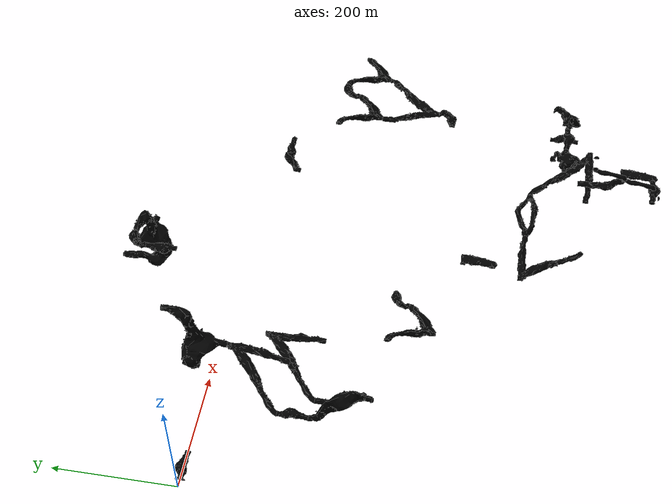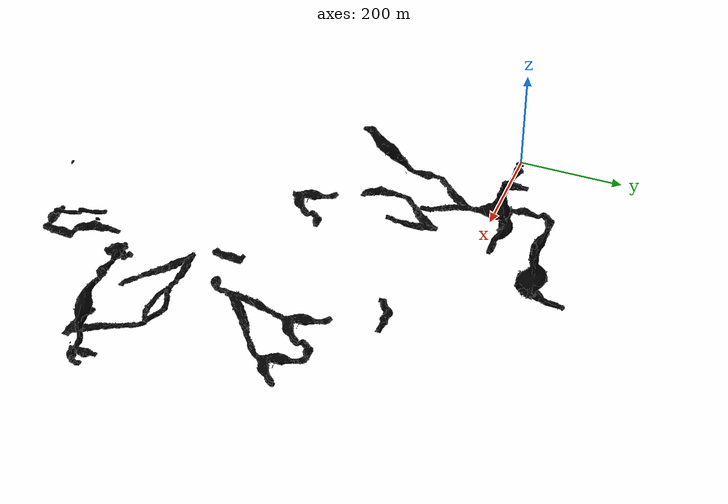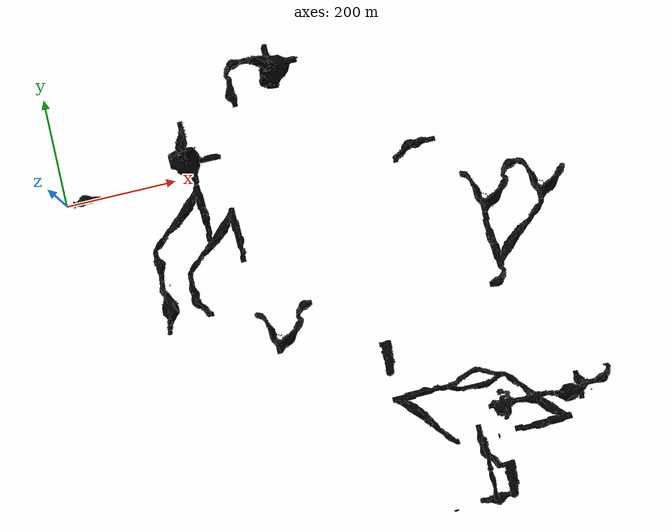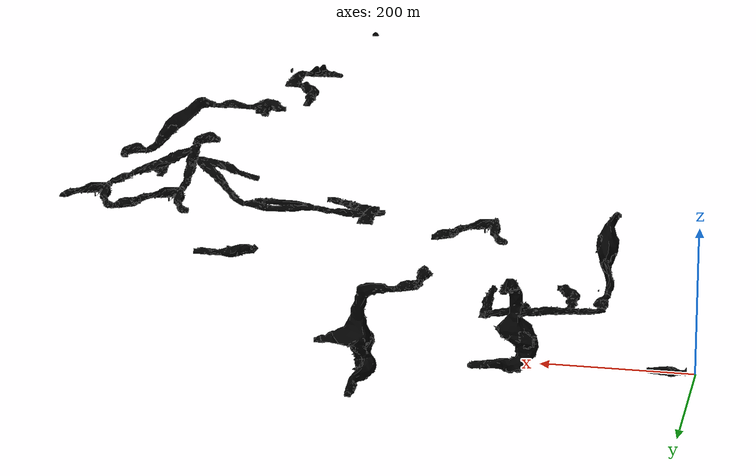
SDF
<sdf version="1.6">
 <world name="cave_circuit_04">
  <physics name="1ms" type="ode">
   <max_step_size>0.004</max_step_size>
   <real_time_factor>1</real_time_factor>
   <real_time_update_rate>1000</real_time_update_rate>
  </physics>
  <scene>
   <ambient>0.1 0.1 0.1 1</ambient>
   <background>0 0 0 1</background>
   <grid>0</grid>
   <origin_visual>0</origin_visual>
   <shadows>1</shadows>
  </scene>
  <atmosphere type="adiabatic">
   <temperature>288</temperature>
   <temperature_gradient>0.2</temperature_gradient>
  </atmosphere>
  <model name="performer_detector_rockfall_1">
   <static>true</static>
   <pose>761.5 -147.13 129.6 0.0 -3 -0.33</pose>
   <plugin filename="libignition-gazebo-performer-detector-system.so" name="ignition::gazebo::systems::PerformerDetector">
    <topic>/subt_performer_detector</topic>
    <geometry><box><size>20 30 10</size></box></geometry>
   </plugin>
   <plugin name="ignition::gazebo::systems::TriggeredPublisher" filename="libignition-gazebo-triggered-publisher-system.so">
    <input type="ignition.msgs.Pose" topic="/subt_performer_detector">
     <match field="header.data">{key: "frame_id" value: "performer_detector_rockfall_1"}</match>
     <match field="header.data">{key: "state" value: "0"}</match>
    </input>
    <output type="ignition.msgs.Empty" topic="/model/dynamic_rocks_1/breadcrumbs/Rock/deploy"/>
   </plugin>
  </model>
  <model name="performer_detector_rockfall_2">
   <static>true</static>
   <pose>578.29 -568.86 -19.15 0.205 0.0 0.867</pose>
   <plugin filename="libignition-gazebo-performer-detector-system.so" name="ignition::gazebo::systems::PerformerDetector">
    <topic>/subt_performer_detector</topic>
    <geometry><box><size>20 30 10</size></box></geometry>
   </plugin>
   <plugin name="ignition::gazebo::systems::TriggeredPublisher" filename="libignition-gazebo-triggered-publisher-system.so">
    <input type="ignition.msgs.Pose" topic="/subt_performer_detector">
     <match field="header.data">{key: "frame_id" value: "performer_detector_rockfall_2"}</match>
     <match field="header.data">{key: "state" value: "0"}</match>
    </input>
    <output type="ignition.msgs.Empty" topic="/model/dynamic_rocks_2/breadcrumbs/Rock/deploy"/>
   </plugin>
  </model>
  <model name="performer_detector_rockfall_3">
   <static>true</static>
   <pose>393.54 -367.25 42.74 0.13 0 1.547</pose>
   <plugin filename="libignition-gazebo-performer-detector-system.so" name="ignition::gazebo::systems::PerformerDetector">
    <topic>/subt_performer_detector</topic>
    <geometry><box><size>20 30 10</size></box></geometry>
   </plugin>
   <plugin name="ignition::gazebo::systems::TriggeredPublisher" filename="libignition-gazebo-triggered-publisher-system.so">
    <input type="ignition.msgs.Pose" topic="/subt_performer_detector">
     <match field="header.data">{key: "frame_id" value: "performer_detector_rockfall_3"}</match>
     <match field="header.data">{key: "state" value: "1"}</match>
    </input>
    <output type="ignition.msgs.Empty" topic="/model/dynamic_rocks_3/breadcrumbs/Rock/deploy"/>
   </plugin>
  </model>
  <gravity>0 0 -9.8</gravity>
  <magnetic_field>6e-06 2.3e-05 -4.2e-05</magnetic_field>
  <atmosphere type="adiabatic"/>
  <include>
   <uri>https://fuel.ignitionrobotics.org/1.0/OpenRobotics/models/Cave 3 Way Elevation 02 Type A</uri>
   <name>tile_3</name>
   <pose>287.5 -125 25 0 -0 0</pose>
  </include>
  <include>
   <uri>https://fuel.ignitionrobotics.org/1.0/OpenRobotics/models/Cave Corner 02 Type A</uri>
   <name>tile_4</name>
   <pose>187.5 -200 0 0 -0 0</pose>
  </include>
  <include>
   <uri>https://fuel.ignitionrobotics.org/1.0/OpenRobotics/models/Cave 3 Way Elevation 01 Type A</uri>
   <name>tile_7</name>
   <pose>237.5 -75 50 0 -0 0</pose>
  </include>
  <include>
   <uri>https://fuel.ignitionrobotics.org/1.0/OpenRobotics/models/Cave 3 Way Elevation 03 Type A</uri>
   <name>tile_8</name>
   <pose>237.5 25 50 0 -0 0</pose>
  </include>
  <include>
   <uri>https://fuel.ignitionrobotics.org/1.0/OpenRobotics/models/Cave Elevation 02 Type A</uri>
   <name>tile_9</name>
   <pose>137.5 -225 25 0 -0 1.5708</pose>
  </include>
  <include>
   <uri>https://fuel.ignitionrobotics.org/1.0/OpenRobotics/models/Cave Straight Type A</uri>
   <name>tile_10</name>
   <pose>137.85 -150 25 0 -0 0</pose>
  </include>
  <include>
   <uri>https://fuel.ignitionrobotics.org/1.0/OpenRobotics/models/Cave 3 Way 01 Type A</uri>
   <name>tile_28</name>
   <pose>312.5 -325 50 0 -0 0</pose>
  </include>
  <include>
   <uri>https://fuel.ignitionrobotics.org/1.0/OpenRobotics/models/Cave Corner 03 Type A</uri>
   <name>tile_29</name>
   <pose>362.5 -275 50 0 -0 1.57079</pose>
  </include>
  <include>
   <uri>https://fuel.ignitionrobotics.org/1.0/OpenRobotics/models/Cave 2 Way 01 Type A</uri>
   <name>tile_31</name>
   <pose>487.5 -400 25 0 0 -1.5708</pose>
  </include>
  <include>
   <uri>https://fuel.ignitionrobotics.org/1.0/OpenRobotics/models/Cave 3 Way Elevation 02 Type A</uri>
   <name>tile_33</name>
   <pose>537.5 -475 0 0 -0 1.5708</pose>
  </include>
  <include>
   <uri>https://fuel.ignitionrobotics.org/1.0/OpenRobotics/models/Cave Split Type A</uri>
   <name>tile_35</name>
   <pose>637.5 -475 0 0 0 -1.5708</pose>
  </include>
  <include>
   <uri>https://fuel.ignitionrobotics.org/1.0/OpenRobotics/models/Cave 3 Way Elevation 01 Type A</uri>
   <name>tile_36</name>
   <pose>737.5 -575 25 0 0 -1.5708</pose>
  </include>
  <include>
   <uri>https://fuel.ignitionrobotics.org/1.0/OpenRobotics/models/Cave Straight Type A</uri>
   <name>tile_38</name>
   <pose>812.5 -525 25 0 -0 0</pose>
  </include>
  <include>
   <uri>https://fuel.ignitionrobotics.org/1.0/OpenRobotics/models/Cave Corner 03 Type A</uri>
   <name>tile_40</name>
   <pose>862.5 -525 50 0 0 -1.57079</pose>
  </include>
  <include>
   <uri>https://fuel.ignitionrobotics.org/1.0/OpenRobotics/models/Cave Elevation 02 Type A</uri>
   <name>tile_41</name>
   <pose>787.5 -525 50 0 -0 0</pose>
  </include>
  <include>
   <uri>https://fuel.ignitionrobotics.org/1.0/OpenRobotics/models/Cave Vertical Shaft Straight Bottom Type A</uri>
   <name>tile_42</name>
   <pose>612.5 -675 125 0 -0 1.5708</pose>
  </include>
  <include>
   <uri>https://fuel.ignitionrobotics.org/1.0/OpenRobotics/models/Cave Vertical Shaft Cantilevered Type A</uri>
   <name>tile_43</name>
   <pose>612.5 -675 125 0 -0 0</pose>
  </include>
  <include>
   <uri>https://fuel.ignitionrobotics.org/1.0/OpenRobotics/models/Cave Vertical Shaft Cantilevered Type A</uri>
   <name>tile_45</name>
   <pose>612.5 -625 140 0 -0 0</pose>
  </include>
  <include>
   <uri>https://fuel.ignitionrobotics.org/1.0/OpenRobotics/models/Cave Straight Type A</uri>
   <name>tile_46</name>
   <pose>712.5 -525 125 0 0 -1.5708</pose>
  </include>
  <include>
   <uri>https://fuel.ignitionrobotics.org/1.0/OpenRobotics/models/Cave 4 Way 01 Type A</uri>
   <name>tile_48</name>
   <pose>662.5 -525 125 0 -0 0</pose>
  </include>
  <include>
   <uri>https://fuel.ignitionrobotics.org/1.0/OpenRobotics/models/Cave 3 Way Elevation 01 Type A</uri>
   <name>tile_50</name>
   <pose>712.5 -250 150 0 -0 3.14159</pose>
  </include>
  <include>
   <uri>https://fuel.ignitionrobotics.org/1.0/OpenRobotics/models/Cave Corner 03 Type A</uri>
   <name>tile_51</name>
   <pose>712.5 -325 150 0 0 -1.57079</pose>
  </include>
  <include>
   <uri>https://fuel.ignitionrobotics.org/1.0/OpenRobotics/models/Cave 3 Way 01 Type A</uri>
   <name>tile_52</name>
   <pose>812.5 -175 125 0 -0 0</pose>
  </include>
  <include>
   <uri>https://fuel.ignitionrobotics.org/1.0/OpenRobotics/models/Cave Corner 02 Type A</uri>
   <name>tile_53</name>
   <pose>612.5 -575 125 0 -0 0</pose>
  </include>
  <include>
   <uri>https://fuel.ignitionrobotics.org/1.0/OpenRobotics/models/Cave 2 Way 01 Type A</uri>
   <name>tile_54</name>
   <pose>637.5 -650 125 0 0 -1.5708</pose>
  </include>
  <include>
   <uri>https://fuel.ignitionrobotics.org/1.0/OpenRobotics/models/Cave 3 Way 01 Type A</uri>
   <name>tile_55</name>
   <pose>712.5 -175 125 0 -0 0</pose>
  </include>
  <include>
   <uri>https://fuel.ignitionrobotics.org/1.0/OpenRobotics/models/Cave Corner 03 Type A</uri>
   <name>tile_56</name>
   <pose>762.5 -125 125 0 -0 1.57079</pose>
  </include>
  <include>
   <uri>https://fuel.ignitionrobotics.org/1.0/OpenRobotics/models/Cave Corner 02 Type A</uri>
   <name>tile_61</name>
   <pose>637.5 -50 100 0 0 -1.5708</pose>
  </include>
  <include>
   <uri>https://fuel.ignitionrobotics.org/1.0/OpenRobotics/models/Cave 3 Way Elevation 03 Type A</uri>
   <name>tile_76</name>
   <pose>412.5 150 75 0 -0 1.5708</pose>
  </include>
  <include>
   <uri>https://fuel.ignitionrobotics.org/1.0/OpenRobotics/models/Cave Corner 03 Type A</uri>
   <name>tile_78</name>
   <pose>337.5 150 150 0 -0 1.57079</pose>
  </include>
  <include>
   <uri>https://fuel.ignitionrobotics.org/1.0/OpenRobotics/models/Cave Straight Type A</uri>
   <name>tile_79</name>
   <pose>337.5 100 150 0 -0 3.14159</pose>
  </include>
  <include>
   <uri>https://fuel.ignitionrobotics.org/1.0/OpenRobotics/models/Cave Transition Type A to and from Type B</uri>
   <name>tile_115</name>
   <pose>37.5 0 0 0 -0 1.5708</pose>
  </include>
  <include>
   <uri>https://fuel.ignitionrobotics.org/1.0/OpenRobotics/models/Cave Cap Type A</uri>
   <name>tile_117</name>
   <pose>287.5 25 0 0 0 -1.5708</pose>
  </include>
  <include>
   <uri>https://fuel.ignitionrobotics.org/1.0/OpenRobotics/models/Cave Cap Type A</uri>
   <name>tile_121</name>
   <pose>587.5 -675 125 0 -0 1.5708</pose>
  </include>
  <include>
   <uri>https://fuel.ignitionrobotics.org/1.0/OpenRobotics/models/Cave Cap Type A</uri>
   <name>tile_122</name>
   <pose>637.5 -575 165 0 0 -1.5708</pose>
  </include>
  <include>
   <uri>https://fuel.ignitionrobotics.org/1.0/OpenRobotics/models/Cave Cap Type A</uri>
   <name>tile_123</name>
   <pose>662.5 -550 125 0 0 -3.14159</pose>
  </include>
  <include>
   <uri>https://fuel.ignitionrobotics.org/1.0/OpenRobotics/models/Cave Cap Type A</uri>
   <name>tile_124</name>
   <pose>862.275 -150.06 124.994 0 0 0</pose>
  </include>
  <include>
   <uri>https://fuel.ignitionrobotics.org/1.0/OpenRobotics/models/Cave Cap Type A</uri>
   <name>tile_125</name>
   <pose>412.5 200 25 0 -0 0</pose>
  </include>
  <include>
   <uri>https://fuel.ignitionrobotics.org/1.0/OpenRobotics/models/Cave Cap Type A</uri>
   <name>tile_126</name>
   <pose>537.67 -675.074 190 0 -0 3.14159</pose>
  </include>
  <include>
   <uri>https://fuel.ignitionrobotics.org/1.0/OpenRobotics/models/Cave Cap Type A</uri>
   <name>tile_127</name>
   <pose>287.506 -274.988 50.0001 0 -0 1.57164</pose>
  </include>
  <include>
   <uri>https://fuel.ignitionrobotics.org/1.0/OpenRobotics/models/Cave Cap Type A</uri>
   <name>tile_128</name>
   <pose>137.412 -275.006 99.9987 0 0 -3.13769</pose>
  </include>
  <plugin name="ignition::gazebo" filename="dummy">
   <level name="level0">
    <ref>tile_115</ref>
    <pose>37.5 -237.537 82.5 0 0 0</pose>
    <geometry><box><size>337.5 1235.07 485</size></box></geometry>
    <buffer>40</buffer>
   </level>
   <level name="level1">
    <ref>tile_128</ref>
    <pose>137.412 -237.537 82.5 0 0 0</pose>
    <geometry><box><size>337.5 1235.07 485</size></box></geometry>
    <buffer>40</buffer>
   </level>
   <level name="level2">
    <ref>tile_9</ref>
    <pose>137.5 -237.537 82.5 0 0 0</pose>
    <geometry><box><size>337.5 1235.07 485</size></box></geometry>
    <buffer>40</buffer>
   </level>
   <level name="level3">
    <ref>tile_10</ref>
    <pose>137.85 -237.537 82.5 0 0 0</pose>
    <geometry><box><size>337.5 1235.07 485</size></box></geometry>
    <buffer>40</buffer>
   </level>
   <level name="level4">
    <ref>rescue_randy_1</ref>
    <pose>143.017 -237.537 82.5 0 0 0</pose>
    <geometry><box><size>337.5 1235.07 485</size></box></geometry>
    <buffer>40</buffer>
   </level>
   <level name="level5">
    <ref>tile_1</ref>
    <pose>162.5 -237.537 82.5 0 0 0</pose>
    <geometry><box><size>337.5 1235.07 485</size></box></geometry>
    <buffer>40</buffer>
   </level>
   <level name="level6">
    <ref>rope_3</ref>
    <pose>187.48 -237.537 82.5 0 0 0</pose>
    <geometry><box><size>337.5 1235.07 485</size></box></geometry>
    <buffer>40</buffer>
   </level>
   <level name="level7">
    <ref>tile_4</ref>
    <pose>187.5 -237.537 82.5 0 0 0</pose>
    <geometry><box><size>337.5 1235.07 485</size></box></geometry>
    <buffer>40</buffer>
   </level>
   <level name="level8">
    <ref>helmet_2</ref>
    <pose>196.311 -237.537 82.5 0 0 0</pose>
    <geometry><box><size>337.5 1235.07 485</size></box></geometry>
    <buffer>40</buffer>
   </level>
   <level name="level9">
    <ref>rope_2</ref>
    <pose>215.715 -237.537 82.5 0 0 0</pose>
    <geometry><box><size>337.5 1235.07 485</size></box></geometry>
    <buffer>40</buffer>
   </level>
   <level name="level10">
    <ref>tile_5</ref>
    <ref>tile_6</ref>
    <ref>tile_7</ref>
    <ref>tile_8</ref>
    <pose>237.5 -237.537 82.5 0 0 0</pose>
    <geometry><box><size>337.5 1235.07 485</size></box></geometry>
    <buffer>40</buffer>
   </level>
   <level name="level11">
    <ref>tile_2</ref>
    <pose>262.5 -237.537 82.5 0 0 0</pose>
    <geometry><box><size>337.5 1235.07 485</size></box></geometry>
    <buffer>40</buffer>
   </level>
   <level name="level12">
    <ref>helmet_3</ref>
    <pose>271.499 -237.537 82.5 0 0 0</pose>
    <geometry><box><size>337.5 1235.07 485</size></box></geometry>
    <buffer>40</buffer>
   </level>
   <level name="level13">
    <ref>helmet_1</ref>
    <pose>285.22 -237.537 82.5 0 0 0</pose>
    <geometry><box><size>337.5 1235.07 485</size></box></geometry>
    <buffer>40</buffer>
   </level>
   <level name="level14">
    <ref>tile_3</ref>
    <ref>tile_77</ref>
    <ref>tile_117</ref>
    <pose>287.5 -237.537 82.5 0 0 0</pose>
    <geometry><box><size>337.5 1235.07 485</size></box></geometry>
    <buffer>40</buffer>
   </level>
   <level name="level15">
    <ref>tile_127</ref>
    <pose>287.506 -237.537 82.5 0 0 0</pose>
    <geometry><box><size>337.5 1235.07 485</size></box></geometry>
    <buffer>40</buffer>
   </level>
   <level name="level16">
    <ref>backpack_3</ref>
    <pose>293.15 -237.537 82.5 0 0 0</pose>
    <geometry><box><size>337.5 1235.07 485</size></box></geometry>
    <buffer>40</buffer>
   </level>
   <level name="level17">
    <ref>tile_28</ref>
    <ref>tile_80</ref>
    <pose>312.5 -237.537 82.5 0 0 0</pose>
    <geometry><box><size>337.5 1235.07 485</size></box></geometry>
    <buffer>40</buffer>
   </level>
   <level name="level18">
    <ref>tile_23</ref>
    <ref>tile_78</ref>
    <ref>tile_79</ref>
    <pose>337.5 -237.537 82.5 0 0 0</pose>
    <geometry><box><size>337.5 1235.07 485</size></box></geometry>
    <buffer>40</buffer>
   </level>
   <level name="level19">
    <ref>tile_29</ref>
    <pose>362.5 -237.537 82.5 0 0 0</pose>
    <geometry><box><size>337.5 1235.07 485</size></box></geometry>
    <buffer>40</buffer>
   </level>
   <level name="level20">
    <ref>phone_3</ref>
    <pose>362.715 -237.537 82.5 0 0 0</pose>
    <geometry><box><size>337.5 1235.07 485</size></box></geometry>
    <buffer>40</buffer>
   </level>
   <level name="level21">
    <ref>tile_30</ref>
    <pose>387.5 -237.537 82.5 0 0 0</pose>
    <geometry><box><size>337.5 1235.07 485</size></box></geometry>
    <buffer>40</buffer>
   </level>
   <level name="level22">
    <ref>phone_2</ref>
    <pose>410.066 -237.537 82.5 0 0 0</pose>
    <geometry><box><size>337.5 1235.07 485</size></box></geometry>
    <buffer>40</buffer>
   </level>
   <level name="level23">
    <ref>tile_27</ref>
    <ref>tile_76</ref>
    <ref>tile_125</ref>
    <pose>412.5 -237.537 82.5 0 0 0</pose>
    <geometry><box><size>337.5 1235.07 485</size></box></geometry>
    <buffer>40</buffer>
   </level>
   <level name="level24">
    <ref>rescue_randy_4</ref>
    <pose>442.134 -237.537 82.5 0 0 0</pose>
    <geometry><box><size>337.5 1235.07 485</size></box></geometry>
    <buffer>40</buffer>
   </level>
   <level name="level25">
    <ref>tile_32</ref>
    <pose>462.5 -237.537 82.5 0 0 0</pose>
    <geometry><box><size>337.5 1235.07 485</size></box></geometry>
    <buffer>40</buffer>
   </level>
   <level name="level26">
    <ref>tile_31</ref>
    <pose>487.5 -237.537 82.5 0 0 0</pose>
    <geometry><box><size>337.5 1235.07 485</size></box></geometry>
    <buffer>40</buffer>
   </level>
   <level name="level27">
    <ref>helmet_4</ref>
    <pose>497.722 -237.537 82.5 0 0 0</pose>
    <geometry><box><size>337.5 1235.07 485</size></box></geometry>
    <buffer>40</buffer>
   </level>
   <level name="level28">
    <ref>rescue_randy_2</ref>
    <pose>519.652 -237.537 82.5 0 0 0</pose>
    <geometry><box><size>337.5 1235.07 485</size></box></geometry>
    <buffer>40</buffer>
   </level>
   <level name="level29">
    <ref>tile_33</ref>
    <ref>tile_81</ref>
    <pose>537.5 -237.537 82.5 0 0 0</pose>
    <geometry><box><size>337.5 1235.07 485</size></box></geometry>
    <buffer>40</buffer>
   </level>
   <level name="level30">
    <ref>tile_126</ref>
    <pose>537.67 -237.537 82.5 0 0 0</pose>
    <geometry><box><size>337.5 1235.07 485</size></box></geometry>
    <buffer>40</buffer>
   </level>
   <level name="level31">
    <ref>tile_75</ref>
    <pose>562.5 -237.537 82.5 0 0 0</pose>
    <geometry><box><size>337.5 1235.07 485</size></box></geometry>
    <buffer>40</buffer>
   </level>
   <level name="level32">
    <ref>tile_121</ref>
    <pose>587.5 -237.537 82.5 0 0 0</pose>
    <geometry><box><size>337.5 1235.07 485</size></box></geometry>
    <buffer>40</buffer>
   </level>
   <level name="level33">
    <ref>phone_1</ref>
    <pose>599.202 -237.537 82.5 0 0 0</pose>
    <geometry><box><size>337.5 1235.07 485</size></box></geometry>
    <buffer>40</buffer>
   </level>
   <level name="level34">
    <ref>tile_42</ref>
    <ref>tile_43</ref>
    <ref>tile_44</ref>
    <ref>tile_45</ref>
    <ref>tile_47</ref>
    <ref>tile_53</ref>
    <pose>612.5 -237.537 82.5 0 0 0</pose>
    <geometry><box><size>337.5 1235.07 485</size></box></geometry>
    <buffer>40</buffer>
   </level>
   <level name="level35">
    <ref>rope_4</ref>
    <pose>613.37 -237.537 82.5 0 0 0</pose>
    <geometry><box><size>337.5 1235.07 485</size></box></geometry>
    <buffer>40</buffer>
   </level>
   <level name="level36">
    <ref>rope_1</ref>
    <pose>613.657 -237.537 82.5 0 0 0</pose>
    <geometry><box><size>337.5 1235.07 485</size></box></geometry>
    <buffer>40</buffer>
   </level>
   <level name="level37">
    <ref>tile_34</ref>
    <ref>tile_35</ref>
    <ref>tile_54</ref>
    <ref>tile_57</ref>
    <ref>tile_61</ref>
    <ref>tile_62</ref>
    <ref>tile_74</ref>
    <ref>tile_122</ref>
    <pose>637.5 -237.537 82.5 0 0 0</pose>
    <geometry><box><size>337.5 1235.07 485</size></box></geometry>
    <buffer>40</buffer>
   </level>
   <level name="level38">
    <ref>backpack_1</ref>
    <pose>639.547 -237.537 82.5 0 0 0</pose>
    <geometry><box><size>337.5 1235.07 485</size></box></geometry>
    <buffer>40</buffer>
   </level>
   <level name="level39">
    <ref>tile_48</ref>
    <ref>tile_49</ref>
    <ref>tile_123</ref>
    <pose>662.5 -237.537 82.5 0 0 0</pose>
    <geometry><box><size>337.5 1235.07 485</size></box></geometry>
    <buffer>40</buffer>
   </level>
   <level name="level40">
    <ref>backpack_4</ref>
    <pose>686.344 -237.537 82.5 0 0 0</pose>
    <geometry><box><size>337.5 1235.07 485</size></box></geometry>
    <buffer>40</buffer>
   </level>
   <level name="level41">
    <ref>tile_60</ref>
    <pose>687.5 -237.537 82.5 0 0 0</pose>
    <geometry><box><size>337.5 1235.07 485</size></box></geometry>
    <buffer>40</buffer>
   </level>
   <level name="level42">
    <ref>backpack_2</ref>
    <pose>709.305 -237.537 82.5 0 0 0</pose>
    <geometry><box><size>337.5 1235.07 485</size></box></geometry>
    <buffer>40</buffer>
   </level>
   <level name="level43">
    <ref>tile_46</ref>
    <ref>tile_50</ref>
    <ref>tile_51</ref>
    <ref>tile_55</ref>
    <pose>712.5 -237.537 82.5 0 0 0</pose>
    <geometry><box><size>337.5 1235.07 485</size></box></geometry>
    <buffer>40</buffer>
   </level>
   <level name="level44">
    <ref>tile_36</ref>
    <pose>737.5 -237.537 82.5 0 0 0</pose>
    <geometry><box><size>337.5 1235.07 485</size></box></geometry>
    <buffer>40</buffer>
   </level>
   <level name="level45">
    <ref>tile_56</ref>
    <pose>762.5 -237.537 82.5 0 0 0</pose>
    <geometry><box><size>337.5 1235.07 485</size></box></geometry>
    <buffer>40</buffer>
   </level>
   <level name="level46">
    <ref>tile_41</ref>
    <pose>787.5 -237.537 82.5 0 0 0</pose>
    <geometry><box><size>337.5 1235.07 485</size></box></geometry>
    <buffer>40</buffer>
   </level>
   <level name="level47">
    <ref>tile_37</ref>
    <ref>tile_38</ref>
    <ref>tile_52</ref>
    <pose>812.5 -237.537 82.5 0 0 0</pose>
    <geometry><box><size>337.5 1235.07 485</size></box></geometry>
    <buffer>40</buffer>
   </level>
   <level name="level48">
    <ref>rescue_randy_3</ref>
    <pose>835.939 -237.537 82.5 0 0 0</pose>
    <geometry><box><size>337.5 1235.07 485</size></box></geometry>
    <buffer>40</buffer>
   </level>
   <level name="level49">
    <ref>rescue_randy_5</ref>
    <pose>842.586 -237.537 82.5 0 0 0</pose>
    <geometry><box><size>337.5 1235.07 485</size></box></geometry>
    <buffer>40</buffer>
   </level>
   <level name="level50">
    <ref>tile_124</ref>
    <pose>862.275 -237.537 82.5 0 0 0</pose>
    <geometry><box><size>337.5 1235.07 485</size></box></geometry>
    <buffer>40</buffer>
   </level>
   <level name="level51">
    <ref>tile_39</ref>
    <ref>tile_40</ref>
    <pose>862.5 -237.537 82.5 0 0 0</pose>
    <geometry><box><size>337.5 1235.07 485</size></box></geometry>
    <buffer>40</buffer>
   </level>
   <level name="level52">
    <ref>tile_126</ref>
    <pose>450 -675.074 82.5 0 0 0</pose>
    <geometry><box><size>1185 337.5 485</size></box></geometry>
    <buffer>40</buffer>
   </level>
   <level name="level53">
    <ref>tile_42</ref>
    <ref>tile_43</ref>
    <ref>tile_121</ref>
    <pose>450 -675 82.5 0 0 0</pose>
    <geometry><box><size>1185 337.5 485</size></box></geometry>
    <buffer>40</buffer>
   </level>
   <level name="level54">
    <ref>rope_1</ref>
    <pose>450 -671.262 82.5 0 0 0</pose>
    <geometry><box><size>1185 337.5 485</size></box></geometry>
    <buffer>40</buffer>
   </level>
   <level name="level55">
    <ref>tile_54</ref>
    <pose>450 -650 82.5 0 0 0</pose>
    <geometry><box><size>1185 337.5 485</size></box></geometry>
    <buffer>40</buffer>
   </level>
   <level name="level56">
    <ref>tile_45</ref>
    <ref>tile_81</ref>
    <pose>450 -625 82.5 0 0 0</pose>
    <geometry><box><size>1185 337.5 485</size></box></geometry>
    <buffer>40</buffer>
   </level>
   <level name="level57">
    <ref>rescue_randy_2</ref>
    <pose>450 -592.864 82.5 0 0 0</pose>
    <geometry><box><size>1185 337.5 485</size></box></geometry>
    <buffer>40</buffer>
   </level>
   <level name="level58">
    <ref>backpack_1</ref>
    <pose>450 -583.574 82.5 0 0 0</pose>
    <geometry><box><size>1185 337.5 485</size></box></geometry>
    <buffer>40</buffer>
   </level>
   <level name="level59">
    <ref>tile_34</ref>
    <ref>tile_36</ref>
    <ref>tile_37</ref>
    <ref>tile_44</ref>
    <ref>tile_53</ref>
    <ref>tile_122</ref>
    <pose>450 -575 82.5 0 0 0</pose>
    <geometry><box><size>1185 337.5 485</size></box></geometry>
    <buffer>40</buffer>
   </level>
   <level name="level60">
    <ref>tile_123</ref>
    <pose>450 -550 82.5 0 0 0</pose>
    <geometry><box><size>1185 337.5 485</size></box></geometry>
    <buffer>40</buffer>
   </level>
   <level name="level61">
    <ref>tile_38</ref>
    <ref>tile_40</ref>
    <ref>tile_41</ref>
    <ref>tile_46</ref>
    <ref>tile_47</ref>
    <ref>tile_48</ref>
    <pose>450 -525 82.5 0 0 0</pose>
    <geometry><box><size>1185 337.5 485</size></box></geometry>
    <buffer>40</buffer>
   </level>
   <level name="level62">
    <ref>tile_33</ref>
    <ref>tile_35</ref>
    <ref>tile_39</ref>
    <pose>450 -475 82.5 0 0 0</pose>
    <geometry><box><size>1185 337.5 485</size></box></geometry>
    <buffer>40</buffer>
   </level>
   <level name="level63">
    <ref>rescue_randy_3</ref>
    <pose>450 -466.222 82.5 0 0 0</pose>
    <geometry><box><size>1185 337.5 485</size></box></geometry>
    <buffer>40</buffer>
   </level>
   <level name="level64">
    <ref>rope_4</ref>
    <pose>450 -464.653 82.5 0 0 0</pose>
    <geometry><box><size>1185 337.5 485</size></box></geometry>
    <buffer>40</buffer>
   </level>
   <level name="level65">
    <ref>tile_32</ref>
    <pose>450 -425 82.5 0 0 0</pose>
    <geometry><box><size>1185 337.5 485</size></box></geometry>
    <buffer>40</buffer>
   </level>
   <level name="level66">
    <ref>helmet_4</ref>
    <pose>450 -411.849 82.5 0 0 0</pose>
    <geometry><box><size>1185 337.5 485</size></box></geometry>
    <buffer>40</buffer>
   </level>
   <level name="level67">
    <ref>tile_31</ref>
    <ref>tile_49</ref>
    <pose>450 -400 82.5 0 0 0</pose>
    <geometry><box><size>1185 337.5 485</size></box></geometry>
    <buffer>40</buffer>
   </level>
   <level name="level68">
    <ref>tile_30</ref>
    <pose>450 -375 82.5 0 0 0</pose>
    <geometry><box><size>1185 337.5 485</size></box></geometry>
    <buffer>40</buffer>
   </level>
   <level name="level69">
    <ref>tile_28</ref>
    <ref>tile_51</ref>
    <pose>450 -325 82.5 0 0 0</pose>
    <geometry><box><size>1185 337.5 485</size></box></geometry>
    <buffer>40</buffer>
   </level>
   <level name="level70">
    <ref>phone_3</ref>
    <pose>450 -289.593 82.5 0 0 0</pose>
    <geometry><box><size>1185 337.5 485</size></box></geometry>
    <buffer>40</buffer>
   </level>
   <level name="level71">
    <ref>backpack_3</ref>
    <pose>450 -278.946 82.5 0 0 0</pose>
    <geometry><box><size>1185 337.5 485</size></box></geometry>
    <buffer>40</buffer>
   </level>
   <level name="level72">
    <ref>backpack_2</ref>
    <pose>450 -278.678 82.5 0 0 0</pose>
    <geometry><box><size>1185 337.5 485</size></box></geometry>
    <buffer>40</buffer>
   </level>
   <level name="level73">
    <ref>tile_128</ref>
    <pose>450 -275.006 82.5 0 0 0</pose>
    <geometry><box><size>1185 337.5 485</size></box></geometry>
    <buffer>40</buffer>
   </level>
   <level name="level74">
    <ref>tile_29</ref>
    <pose>450 -275 82.5 0 0 0</pose>
    <geometry><box><size>1185 337.5 485</size></box></geometry>
    <buffer>40</buffer>
   </level>
   <level name="level75">
    <ref>tile_127</ref>
    <pose>450 -274.988 82.5 0 0 0</pose>
    <geometry><box><size>1185 337.5 485</size></box></geometry>
    <buffer>40</buffer>
   </level>
   <level name="level76">
    <ref>tile_5</ref>
    <ref>tile_27</ref>
    <ref>tile_50</ref>
    <pose>450 -250 82.5 0 0 0</pose>
    <geometry><box><size>1185 337.5 485</size></box></geometry>
    <buffer>40</buffer>
   </level>
   <level name="level77">
    <ref>tile_9</ref>
    <ref>tile_23</ref>
    <pose>450 -225 82.5 0 0 0</pose>
    <geometry><box><size>1185 337.5 485</size></box></geometry>
    <buffer>40</buffer>
   </level>
   <level name="level78">
    <ref>tile_4</ref>
    <pose>450 -200 82.5 0 0 0</pose>
    <geometry><box><size>1185 337.5 485</size></box></geometry>
    <buffer>40</buffer>
   </level>
   <level name="level79">
    <ref>rescue_randy_5</ref>
    <pose>450 -181.972 82.5 0 0 0</pose>
    <geometry><box><size>1185 337.5 485</size></box></geometry>
    <buffer>40</buffer>
   </level>
   <level name="level80">
    <ref>tile_6</ref>
    <ref>tile_52</ref>
    <ref>tile_55</ref>
    <pose>450 -175 82.5 0 0 0</pose>
    <geometry><box><size>1185 337.5 485</size></box></geometry>
    <buffer>40</buffer>
   </level>
   <level name="level81">
    <ref>rope_3</ref>
    <pose>450 -169.875 82.5 0 0 0</pose>
    <geometry><box><size>1185 337.5 485</size></box></geometry>
    <buffer>40</buffer>
   </level>
   <level name="level82">
    <ref>tile_124</ref>
    <pose>450 -150.06 82.5 0 0 0</pose>
    <geometry><box><size>1185 337.5 485</size></box></geometry>
    <buffer>40</buffer>
   </level>
   <level name="level83">
    <ref>tile_10</ref>
    <pose>450 -150 82.5 0 0 0</pose>
    <geometry><box><size>1185 337.5 485</size></box></geometry>
    <buffer>40</buffer>
   </level>
   <level name="level84">
    <ref>rescue_randy_1</ref>
    <pose>450 -145.658 82.5 0 0 0</pose>
    <geometry><box><size>1185 337.5 485</size></box></geometry>
    <buffer>40</buffer>
   </level>
   <level name="level85">
    <ref>helmet_1</ref>
    <pose>450 -126.712 82.5 0 0 0</pose>
    <geometry><box><size>1185 337.5 485</size></box></geometry>
    <buffer>40</buffer>
   </level>
   <level name="level86">
    <ref>tile_3</ref>
    <ref>tile_56</ref>
    <ref>tile_57</ref>
    <pose>450 -125 82.5 0 0 0</pose>
    <geometry><box><size>1185 337.5 485</size></box></geometry>
    <buffer>40</buffer>
   </level>
   <level name="level87">
    <ref>tile_7</ref>
    <pose>450 -75 82.5 0 0 0</pose>
    <geometry><box><size>1185 337.5 485</size></box></geometry>
    <buffer>40</buffer>
   </level>
   <level name="level88">
    <ref>tile_2</ref>
    <ref>tile_60</ref>
    <ref>tile_61</ref>
    <pose>450 -50 82.5 0 0 0</pose>
    <geometry><box><size>1185 337.5 485</size></box></geometry>
    <buffer>40</buffer>
   </level>
   <level name="level89">
    <ref>backpack_4</ref>
    <pose>450 -44.4365 82.5 0 0 0</pose>
    <geometry><box><size>1185 337.5 485</size></box></geometry>
    <buffer>40</buffer>
   </level>
   <level name="level90">
    <ref>tile_1</ref>
    <ref>tile_62</ref>
    <ref>tile_115</ref>
    <pose>450 0 82.5 0 0 0</pose>
    <geometry><box><size>1185 337.5 485</size></box></geometry>
    <buffer>40</buffer>
   </level>
   <level name="level91">
    <ref>helmet_2</ref>
    <pose>450 5.28961 82.5 0 0 0</pose>
    <geometry><box><size>1185 337.5 485</size></box></geometry>
    <buffer>40</buffer>
   </level>
   <level name="level92">
    <ref>tile_8</ref>
    <ref>tile_117</ref>
    <pose>450 25 82.5 0 0 0</pose>
    <geometry><box><size>1185 337.5 485</size></box></geometry>
    <buffer>40</buffer>
   </level>
   <level name="level93">
    <ref>rope_2</ref>
    <pose>450 36.6224 82.5 0 0 0</pose>
    <geometry><box><size>1185 337.5 485</size></box></geometry>
    <buffer>40</buffer>
   </level>
   <level name="level94">
    <ref>tile_80</ref>
    <pose>450 50 82.5 0 0 0</pose>
    <geometry><box><size>1185 337.5 485</size></box></geometry>
    <buffer>40</buffer>
   </level>
   <level name="level95">
    <ref>tile_74</ref>
    <pose>450 75 82.5 0 0 0</pose>
    <geometry><box><size>1185 337.5 485</size></box></geometry>
    <buffer>40</buffer>
   </level>
   <level name="level96">
    <ref>tile_77</ref>
    <ref>tile_79</ref>
    <pose>450 100 82.5 0 0 0</pose>
    <geometry><box><size>1185 337.5 485</size></box></geometry>
    <buffer>40</buffer>
   </level>
   <level name="level97">
    <ref>helmet_3</ref>
    <pose>450 100.481 82.5 0 0 0</pose>
    <geometry><box><size>1185 337.5 485</size></box></geometry>
    <buffer>40</buffer>
   </level>
   <level name="level98">
    <ref>phone_2</ref>
    <pose>450 139.655 82.5 0 0 0</pose>
    <geometry><box><size>1185 337.5 485</size></box></geometry>
    <buffer>40</buffer>
   </level>
   <level name="level99">
    <ref>tile_75</ref>
    <ref>tile_76</ref>
    <ref>tile_78</ref>
    <pose>450 150 82.5 0 0 0</pose>
    <geometry><box><size>1185 337.5 485</size></box></geometry>
    <buffer>40</buffer>
   </level>
   <level name="level100">
    <ref>rescue_randy_4</ref>
    <pose>450 153.075 82.5 0 0 0</pose>
    <geometry><box><size>1185 337.5 485</size></box></geometry>
    <buffer>40</buffer>
   </level>
   <level name="level101">
    <ref>phone_1</ref>
    <pose>450 154.454 82.5 0 0 0</pose>
    <geometry><box><size>1185 337.5 485</size></box></geometry>
    <buffer>40</buffer>
   </level>
   <level name="level102">
    <ref>tile_125</ref>
    <pose>450 200 82.5 0 0 0</pose>
    <geometry><box><size>1185 337.5 485</size></box></geometry>
    <buffer>40</buffer>
   </level>
  </plugin>
 </world>
</sdf>

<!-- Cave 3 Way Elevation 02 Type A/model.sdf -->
<sdf version="1.6">
  <model name="Cave 3 Way Elevation 02 Type A">
    <static>true</static>
    <link name="base_link">
      <collision name="collision">
        <pose>0 0 0 0 0 0</pose>
        <geometry>
          <mesh>
            <uri>model://Cave 3 Way Elevation 02 Type A/meshes/3wayelevation02.dae</uri>
            <scale>1.0 1.0 1.0</scale>
          </mesh>
        </geometry>
      </collision>
      <visual name="CaveWall_visual">
        <geometry>
          <mesh>
            <uri>model://Cave 3 Way Elevation 02 Type A/meshes/3wayelevation02.dae</uri>
            <submesh>
              <name>CaveWall</name>
              <center>false</center>
            </submesh>
          </mesh>
        </geometry>
        <material>
          <diffuse>0 0 0 1</diffuse>
          <specular>0 0 0 1</specular>
          <pbr>
            <metal>
              <albedo_map>model://Cave 3 Way Elevation 02 Type A/materials/textures/CaveWall_Albedo.png</albedo_map>
              <normal_map>model://Cave 3 Way Elevation 02 Type A/materials/textures/CaveWall_Normal.png</normal_map>
              <roughness_map>model://Cave 3 Way Elevation 02 Type A/materials/textures/CaveWall_Roughness.png</roughness_map>
            </metal>
          </pbr>

          <script>
            <uri>model://Cave 3 Way Elevation 02 Type A/materials/scripts/</uri>
            <uri>model://Cave 3 Way Elevation 02 Type A/materials/textures/</uri>
            <name>CaveTile/CaveWall_Diffuse</name>
          </script>
        </material>
      </visual>
      <visual name="Gravel_visual">
        <geometry>
          <mesh>
            <uri>model://Cave 3 Way Elevation 02 Type A/meshes/3wayelevation02.dae</uri>
            <submesh>
              <name>Gravel</name>
              <center>false</center>
            </submesh>
          </mesh>
        </geometry>
        <material>
          <diffuse>0 0 0 1</diffuse>
          <specular>0 0 0 1</specular>
          <pbr>
            <metal>
              <albedo_map>model://Cave 3 Way Elevation 02 Type A/materials/textures/Gravel_Albedo.png</albedo_map>
              <normal_map>model://Cave 3 Way Elevation 02 Type A/materials/textures/Gravel_Normal.png</normal_map>
              <roughness_map>model://Cave 3 Way Elevation 02 Type A/materials/textures/Gravel_Roughness.png</roughness_map>
            </metal>
          </pbr>

          <script>
            <uri>model://Cave 3 Way Elevation 02 Type A/materials/scripts/</uri>
            <uri>model://Cave 3 Way Elevation 02 Type A/materials/textures/</uri>
            <name>CaveTile/Gravel_Diffuse</name>
          </script>
        </material>
      </visual>
      <visual name="StriatedRock_visual">
        <geometry>
          <mesh>
            <uri>model://Cave 3 Way Elevation 02 Type A/meshes/3wayelevation02.dae</uri>
            <submesh>
              <name>StriatedRock</name>
              <center>false</center>
            </submesh>
          </mesh>
        </geometry>
        <material>
          <diffuse>0 0 0 1</diffuse>
          <specular>0 0 0 1</specular>
          <pbr>
            <metal>
              <albedo_map>model://Cave 3 Way Elevation 02 Type A/materials/textures/StriatedRock_Albedo.png</albedo_map>
              <normal_map>model://Cave 3 Way Elevation 02 Type A/materials/textures/StriatedRock_Normal.png</normal_map>
              <roughness_map>model://Cave 3 Way Elevation 02 Type A/materials/textures/StriatedRock_Roughness.png</roughness_map>
            </metal>
          </pbr>

          <script>
            <uri>model://Cave 3 Way Elevation 02 Type A/materials/scripts/</uri>
            <uri>model://Cave 3 Way Elevation 02 Type A/materials/textures/</uri>
            <name>CaveTile/StriatedRock_Diffuse</name>
          </script>
        </material>
      </visual>
      <visual name="RockPile_visual">
        <geometry>
          <mesh>
            <uri>model://Cave 3 Way Elevation 02 Type A/meshes/3wayelevation02.dae</uri>
            <submesh>
              <name>RockPile</name>
              <center>false</center>
            </submesh>
          </mesh>
        </geometry>
        <material>
          <diffuse>0 0 0 1</diffuse>
          <specular>0 0 0 1</specular>
          <pbr>
            <metal>
              <albedo_map>model://Cave 3 Way Elevation 02 Type A/materials/textures/RockPile_Albedo.png</albedo_map>
              <normal_map>model://Cave 3 Way Elevation 02 Type A/materials/textures/RockPile_Normal.png</normal_map>
              <roughness_map>model://Cave 3 Way Elevation 02 Type A/materials/textures/RockPile_Roughness.png</roughness_map>
            </metal>
          </pbr>

          <script>
            <uri>model://Cave 3 Way Elevation 02 Type A/materials/scripts/</uri>
            <uri>model://Cave 3 Way Elevation 02 Type A/materials/textures/</uri>
            <name>CaveTile/RockPile_Diffuse</name>
          </script>
        </material>
      </visual>
    </link>

    <plugin filename="libignition-gazebo-performer-detector-system.so" name="ignition::gazebo::systems::PerformerDetector">
      <topic>/subt_performer_detector</topic>
      <pose>-3.2 42.5 1.7 0 0 0</pose>
      <header_data>
        <key>type</key>
        <value>decision</value>
      </header_data>
      <geometry>
        <box>
          <size>15 15 7</size>
        </box>
      </geometry>
    </plugin>
    <plugin filename="libignition-gazebo-performer-detector-system.so" name="ignition::gazebo::systems::PerformerDetector">
      <topic>/subt_performer_detector</topic>
      <pose>-50 0 -6.5 0 0 0</pose>
      <header_data>
        <key>type</key>
        <value>elevation</value>
      </header_data>
      <geometry>
        <box>
          <size>40 40 20</size>
        </box>
      </geometry>
    </plugin>
  </model>
</sdf>

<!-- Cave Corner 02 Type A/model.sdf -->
<sdf version="1.6">
  <model name="Cave Corner 02 Type A">
    <static>true</static>
    <link name="base_link">
      <collision name="collision">
        <pose>0 0 0 0 0 0</pose>
        <geometry>
          <mesh>
            <uri>model://Cave Corner 02 Type A/meshes/corner02.dae</uri>
            <scale>1.0 1.0 1.0</scale>
          </mesh>
        </geometry>
      </collision>
      <visual name="Gravel_visual">
        <geometry>
          <mesh>
            <uri>model://Cave Corner 02 Type A/meshes/corner02.dae</uri>
            <submesh>
              <name>Gravel</name>
              <center>false</center>
            </submesh>
          </mesh>
        </geometry>
        <material>
          <diffuse>0 0 0 1</diffuse>
          <specular>0 0 0 1</specular>
          <pbr>
            <metal>
              <albedo_map>model://Cave Corner 02 Type A/materials/textures/Gravel_Albedo.png</albedo_map>
              <normal_map>model://Cave Corner 02 Type A/materials/textures/Gravel_Normal.png</normal_map>
              <roughness_map>model://Cave Corner 02 Type A/materials/textures/Gravel_Roughness.png</roughness_map>
            </metal>
          </pbr>

          <script>
            <uri>model://Cave Corner 02 Type A/materials/scripts/</uri>
            <uri>model://Cave Corner 02 Type A/materials/textures/</uri>
            <name>CaveTile/Gravel_Diffuse</name>
          </script>
        </material>
      </visual>
      <visual name="RockPile_visual">
        <geometry>
          <mesh>
            <uri>model://Cave Corner 02 Type A/meshes/corner02.dae</uri>
            <submesh>
              <name>RockPile</name>
              <center>false</center>
            </submesh>
          </mesh>
        </geometry>
        <material>
          <diffuse>0 0 0 1</diffuse>
          <specular>0 0 0 1</specular>
          <pbr>
            <metal>
              <albedo_map>model://Cave Corner 02 Type A/materials/textures/RockPile_Albedo.png</albedo_map>
              <normal_map>model://Cave Corner 02 Type A/materials/textures/RockPile_Normal.png</normal_map>
              <roughness_map>model://Cave Corner 02 Type A/materials/textures/RockPile_Roughness.png</roughness_map>
            </metal>
          </pbr>

          <script>
            <uri>model://Cave Corner 02 Type A/materials/scripts/</uri>
            <uri>model://Cave Corner 02 Type A/materials/textures/</uri>
            <name>CaveTile/RockPile_Diffuse</name>
          </script>
        </material>
      </visual>
      <visual name="StriatedRock_visual">
        <geometry>
          <mesh>
            <uri>model://Cave Corner 02 Type A/meshes/corner02.dae</uri>
            <submesh>
              <name>StriatedRock</name>
              <center>false</center>
            </submesh>
          </mesh>
        </geometry>
        <material>
          <diffuse>0 0 0 1</diffuse>
          <specular>0 0 0 1</specular>
          <pbr>
            <metal>
              <albedo_map>model://Cave Corner 02 Type A/materials/textures/StriatedRock_Albedo.png</albedo_map>
              <normal_map>model://Cave Corner 02 Type A/materials/textures/StriatedRock_Normal.png</normal_map>
              <roughness_map>model://Cave Corner 02 Type A/materials/textures/StriatedRock_Roughness.png</roughness_map>
            </metal>
          </pbr>

          <script>
            <uri>model://Cave Corner 02 Type A/materials/scripts/</uri>
            <uri>model://Cave Corner 02 Type A/materials/textures/</uri>
            <name>CaveTile/StriatedRock_Diffuse</name>
          </script>
        </material>
      </visual>
      <visual name="CaveWall_visual">
        <geometry>
          <mesh>
            <uri>model://Cave Corner 02 Type A/meshes/corner02.dae</uri>
            <submesh>
              <name>CaveWall</name>
              <center>false</center>
            </submesh>
          </mesh>
        </geometry>
        <material>
          <diffuse>0 0 0 1</diffuse>
          <specular>0 0 0 1</specular>
          <pbr>
            <metal>
              <albedo_map>model://Cave Corner 02 Type A/materials/textures/CaveWall_Albedo.png</albedo_map>
              <normal_map>model://Cave Corner 02 Type A/materials/textures/CaveWall_Normal.png</normal_map>
              <roughness_map>model://Cave Corner 02 Type A/materials/textures/CaveWall_Roughness.png</roughness_map>
            </metal>
          </pbr>

          <script>
            <uri>model://Cave Corner 02 Type A/materials/scripts/</uri>
            <uri>model://Cave Corner 02 Type A/materials/textures/</uri>
            <name>CaveTile/CaveWall_Diffuse</name>
          </script>
        </material>
      </visual>
    </link>
  </model>
</sdf>

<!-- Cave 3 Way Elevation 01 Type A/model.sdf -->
<sdf version="1.6">
  <model name="Cave 3 Way Elevation 01 Type A">
    <static>true</static>
    <link name="base_link">
      <collision name="collision">
        <pose>0 0 0 0 0 0</pose>
        <geometry>
          <mesh>
            <uri>model://Cave 3 Way Elevation 01 Type A/meshes/3wayelevation01.dae</uri>
            <scale>1.0 1.0 1.0</scale>
          </mesh>
        </geometry>
      </collision>
      <visual name="CaveWall_visual">
        <geometry>
          <mesh>
            <uri>model://Cave 3 Way Elevation 01 Type A/meshes/3wayelevation01.dae</uri>
            <submesh>
              <name>CaveWall</name>
              <center>false</center>
            </submesh>
          </mesh>
        </geometry>
        <material>
          <diffuse>0 0 0 1</diffuse>
          <specular>0 0 0 1</specular>
          <pbr>
            <metal>
              <albedo_map>model://Cave 3 Way Elevation 01 Type A/materials/textures/CaveWall_Albedo.png</albedo_map>
              <normal_map>model://Cave 3 Way Elevation 01 Type A/materials/textures/CaveWall_Normal.png</normal_map>
              <roughness_map>model://Cave 3 Way Elevation 01 Type A/materials/textures/CaveWall_Roughness.png</roughness_map>
            </metal>
          </pbr>

          <script>
            <uri>model://Cave 3 Way Elevation 01 Type A/materials/scripts/</uri>
            <uri>model://Cave 3 Way Elevation 01 Type A/materials/textures/</uri>
            <name>CaveTile/CaveWall_Diffuse</name>
          </script>
        </material>
      </visual>
      <visual name="Gravel_visual">
        <geometry>
          <mesh>
            <uri>model://Cave 3 Way Elevation 01 Type A/meshes/3wayelevation01.dae</uri>
            <submesh>
              <name>Gravel</name>
              <center>false</center>
            </submesh>
          </mesh>
        </geometry>
        <material>
          <diffuse>0 0 0 1</diffuse>
          <specular>0 0 0 1</specular>
          <pbr>
            <metal>
              <albedo_map>model://Cave 3 Way Elevation 01 Type A/materials/textures/Gravel_Albedo.png</albedo_map>
              <normal_map>model://Cave 3 Way Elevation 01 Type A/materials/textures/Gravel_Normal.png</normal_map>
              <roughness_map>model://Cave 3 Way Elevation 01 Type A/materials/textures/Gravel_Roughness.png</roughness_map>
            </metal>
          </pbr>

          <script>
            <uri>model://Cave 3 Way Elevation 01 Type A/materials/scripts/</uri>
            <uri>model://Cave 3 Way Elevation 01 Type A/materials/textures/</uri>
            <name>CaveTile/Gravel_Diffuse</name>
          </script>
        </material>
      </visual>
      <visual name="StriatedRock_visual">
        <geometry>
          <mesh>
            <uri>model://Cave 3 Way Elevation 01 Type A/meshes/3wayelevation01.dae</uri>
            <submesh>
              <name>StriatedRock</name>
              <center>false</center>
            </submesh>
          </mesh>
        </geometry>
        <material>
          <diffuse>0 0 0 1</diffuse>
          <specular>0 0 0 1</specular>
          <pbr>
            <metal>
              <albedo_map>model://Cave 3 Way Elevation 01 Type A/materials/textures/StriatedRock_Albedo.png</albedo_map>
              <normal_map>model://Cave 3 Way Elevation 01 Type A/materials/textures/StriatedRock_Normal.png</normal_map>
              <roughness_map>model://Cave 3 Way Elevation 01 Type A/materials/textures/StriatedRock_Roughness.png</roughness_map>
            </metal>
          </pbr>

          <script>
            <uri>model://Cave 3 Way Elevation 01 Type A/materials/scripts/</uri>
            <uri>model://Cave 3 Way Elevation 01 Type A/materials/textures/</uri>
            <name>CaveTile/StriatedRock_Diffuse</name>
          </script>
        </material>
      </visual>
      <visual name="RockPile_visual">
        <geometry>
          <mesh>
            <uri>model://Cave 3 Way Elevation 01 Type A/meshes/3wayelevation01.dae</uri>
            <submesh>
              <name>RockPile</name>
              <center>false</center>
            </submesh>
          </mesh>
        </geometry>
        <material>
          <diffuse>0 0 0 1</diffuse>
          <specular>0 0 0 1</specular>
          <pbr>
            <metal>
              <albedo_map>model://Cave 3 Way Elevation 01 Type A/materials/textures/RockPile_Albedo.png</albedo_map>
              <normal_map>model://Cave 3 Way Elevation 01 Type A/materials/textures/RockPile_Normal.png</normal_map>
              <roughness_map>model://Cave 3 Way Elevation 01 Type A/materials/textures/RockPile_Roughness.png</roughness_map>
            </metal>
          </pbr>

          <script>
            <uri>model://Cave 3 Way Elevation 01 Type A/materials/scripts/</uri>
            <uri>model://Cave 3 Way Elevation 01 Type A/materials/textures/</uri>
            <name>CaveTile/RockPile_Diffuse</name>
          </script>
        </material>
      </visual>
    </link>

    <plugin filename="libignition-gazebo-performer-detector-system.so" name="ignition::gazebo::systems::PerformerDetector">
      <topic>/subt_performer_detector</topic>
      <pose>-3.2 42.5 1.7 0 0 0</pose>
      <header_data>
        <key>type</key>
        <value>decision</value>
      </header_data>
      <geometry>
        <box>
          <size>15 15 7</size>
        </box>
      </geometry>
    </plugin>
    <plugin filename="libignition-gazebo-performer-detector-system.so" name="ignition::gazebo::systems::PerformerDetector">
      <topic>/subt_performer_detector</topic>
      <pose>-50 0 -6.5 0 0 0</pose>
      <header_data>
        <key>type</key>
        <value>elevation</value>
      </header_data>
      <geometry>
        <box>
          <size>40 40 20</size>
        </box>
      </geometry>
    </plugin>
  </model>
</sdf>

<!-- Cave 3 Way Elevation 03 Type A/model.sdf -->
<sdf version="1.6">
  <model name="Cave 3 Way Elevation 03 Type A">
    <static>true</static>
    <link name="base_link">
      <collision name="collision">
        <pose>0 0 0 0 0 0</pose>
        <geometry>
          <mesh>
            <uri>model://Cave 3 Way Elevation 03 Type A/meshes/3wayelevation03.dae</uri>
            <scale>1.0 1.0 1.0</scale>
          </mesh>
        </geometry>
      </collision>
      <visual name="Gravel_visual">
        <geometry>
          <mesh>
            <uri>model://Cave 3 Way Elevation 03 Type A/meshes/3wayelevation03.dae</uri>
            <submesh>
              <name>Gravel</name>
              <center>false</center>
            </submesh>
          </mesh>
        </geometry>
        <material>
          <diffuse>0 0 0 1</diffuse>
          <specular>0 0 0 1</specular>
          <pbr>
            <metal>
              <albedo_map>model://Cave 3 Way Elevation 03 Type A/materials/textures/Gravel_Albedo.png</albedo_map>
              <normal_map>model://Cave 3 Way Elevation 03 Type A/materials/textures/Gravel_Normal.png</normal_map>
              <roughness_map>model://Cave 3 Way Elevation 03 Type A/materials/textures/Gravel_Roughness.png</roughness_map>
            </metal>
          </pbr>

          <script>
            <uri>model://Cave 3 Way Elevation 03 Type A/materials/scripts/</uri>
            <uri>model://Cave 3 Way Elevation 03 Type A/materials/textures/</uri>
            <name>CaveTile/Gravel_Diffuse</name>
          </script>
        </material>
      </visual>
      <visual name="StriatedRock_visual">
        <geometry>
          <mesh>
            <uri>model://Cave 3 Way Elevation 03 Type A/meshes/3wayelevation03.dae</uri>
            <submesh>
              <name>StriatedRock</name>
              <center>false</center>
            </submesh>
          </mesh>
        </geometry>
        <material>
          <diffuse>0 0 0 1</diffuse>
          <specular>0 0 0 1</specular>
          <pbr>
            <metal>
              <albedo_map>model://Cave 3 Way Elevation 03 Type A/materials/textures/StriatedRock_Albedo.png</albedo_map>
              <normal_map>model://Cave 3 Way Elevation 03 Type A/materials/textures/StriatedRock_Normal.png</normal_map>
              <roughness_map>model://Cave 3 Way Elevation 03 Type A/materials/textures/StriatedRock_Roughness.png</roughness_map>
            </metal>
          </pbr>

          <script>
            <uri>model://Cave 3 Way Elevation 03 Type A/materials/scripts/</uri>
            <uri>model://Cave 3 Way Elevation 03 Type A/materials/textures/</uri>
            <name>CaveTile/StriatedRock_Diffuse</name>
          </script>
        </material>
      </visual>
      <visual name="RockPile_visual">
        <geometry>
          <mesh>
            <uri>model://Cave 3 Way Elevation 03 Type A/meshes/3wayelevation03.dae</uri>
            <submesh>
              <name>RockPile</name>
              <center>false</center>
            </submesh>
          </mesh>
        </geometry>
        <material>
          <diffuse>0 0 0 1</diffuse>
          <specular>0 0 0 1</specular>
          <pbr>
            <metal>
              <albedo_map>model://Cave 3 Way Elevation 03 Type A/materials/textures/RockPile_Albedo.png</albedo_map>
              <normal_map>model://Cave 3 Way Elevation 03 Type A/materials/textures/RockPile_Normal.png</normal_map>
              <roughness_map>model://Cave 3 Way Elevation 03 Type A/materials/textures/RockPile_Roughness.png</roughness_map>
            </metal>
          </pbr>

          <script>
            <uri>model://Cave 3 Way Elevation 03 Type A/materials/scripts/</uri>
            <uri>model://Cave 3 Way Elevation 03 Type A/materials/textures/</uri>
            <name>CaveTile/RockPile_Diffuse</name>
          </script>
        </material>
      </visual>
      <visual name="CaveWall_visual">
        <geometry>
          <mesh>
            <uri>model://Cave 3 Way Elevation 03 Type A/meshes/3wayelevation03.dae</uri>
            <submesh>
              <name>CaveWall</name>
              <center>false</center>
            </submesh>
          </mesh>
        </geometry>
        <material>
          <diffuse>0 0 0 1</diffuse>
          <specular>0 0 0 1</specular>
          <pbr>
            <metal>
              <albedo_map>model://Cave 3 Way Elevation 03 Type A/materials/textures/CaveWall_Albedo.png</albedo_map>
              <normal_map>model://Cave 3 Way Elevation 03 Type A/materials/textures/CaveWall_Normal.png</normal_map>
              <roughness_map>model://Cave 3 Way Elevation 03 Type A/materials/textures/CaveWall_Roughness.png</roughness_map>
            </metal>
          </pbr>

          <script>
            <uri>model://Cave 3 Way Elevation 03 Type A/materials/scripts/</uri>
            <uri>model://Cave 3 Way Elevation 03 Type A/materials/textures/</uri>
            <name>CaveTile/CaveWall_Diffuse</name>
          </script>
        </material>
      </visual>
    </link>

    <plugin filename="libignition-gazebo-performer-detector-system.so" name="ignition::gazebo::systems::PerformerDetector">
      <topic>/subt_performer_detector</topic>
      <pose>-25 5 -30 0 0 0</pose>
      <header_data>
        <key>type</key>
        <value>vertical</value>
      </header_data>
      <geometry>
        <box>
          <size>25 25 10</size>
        </box>
      </geometry>
    </plugin>

    <plugin filename="libignition-gazebo-performer-detector-system.so" name="ignition::gazebo::systems::PerformerDetector">
      <topic>/subt_performer_detector</topic>
      <pose>-10 5 50 0 0 0</pose>
      <header_data>
        <key>type</key>
        <value>vertical</value>
      </header_data>
      <geometry>
        <box>
          <size>25 25 30</size>
        </box>
      </geometry>
    </plugin>

    <plugin filename="libignition-gazebo-performer-detector-system.so" name="ignition::gazebo::systems::PerformerDetector">
      <topic>/subt_performer_detector</topic>
      <pose>-10 0 0 0 0 0</pose>
      <header_data>
        <key>type</key>
        <value>decision, vertical</value>
      </header_data>
      <geometry>
        <box>
          <size>50 30 30</size>
        </box>
      </geometry>
    </plugin>
  </model>
</sdf>

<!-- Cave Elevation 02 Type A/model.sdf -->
<sdf version="1.6">
  <model name="Cave Elevation 02 Type A">
    <static>true</static>
    <link name="base_link">
      <collision name="collision">
        <pose>0 0 0 0 0 0</pose>
        <geometry>
          <mesh>
            <uri>model://Cave Elevation 02 Type A/meshes/elevation02.dae</uri>
            <scale>1.0 1.0 1.0</scale>
          </mesh>
        </geometry>
      </collision>
      <visual name="Gravel_visual">
        <geometry>
          <mesh>
            <uri>model://Cave Elevation 02 Type A/meshes/elevation02.dae</uri>
            <submesh>
              <name>Gravel</name>
              <center>false</center>
            </submesh>
          </mesh>
        </geometry>
        <material>
          <diffuse>0 0 0 1</diffuse>
          <specular>0 0 0 1</specular>
          <pbr>
            <metal>
              <albedo_map>model://Cave Elevation 02 Type A/materials/textures/Gravel_Albedo.png</albedo_map>
              <normal_map>model://Cave Elevation 02 Type A/materials/textures/Gravel_Normal.png</normal_map>
              <roughness_map>model://Cave Elevation 02 Type A/materials/textures/Gravel_Roughness.png</roughness_map>
            </metal>
          </pbr>

          <script>
            <uri>model://Cave Elevation 02 Type A/materials/scripts/</uri>
            <uri>model://Cave Elevation 02 Type A/materials/textures/</uri>
            <name>CaveTile/Gravel_Diffuse</name>
          </script>
        </material>
      </visual>
      <visual name="RockPile_visual">
        <geometry>
          <mesh>
            <uri>model://Cave Elevation 02 Type A/meshes/elevation02.dae</uri>
            <submesh>
              <name>RockPile</name>
              <center>false</center>
            </submesh>
          </mesh>
        </geometry>
        <material>
          <diffuse>0 0 0 1</diffuse>
          <specular>0 0 0 1</specular>
          <pbr>
            <metal>
              <albedo_map>model://Cave Elevation 02 Type A/materials/textures/RockPile_Albedo.png</albedo_map>
              <normal_map>model://Cave Elevation 02 Type A/materials/textures/RockPile_Normal.png</normal_map>
              <roughness_map>model://Cave Elevation 02 Type A/materials/textures/RockPile_Roughness.png</roughness_map>
            </metal>
          </pbr>

          <script>
            <uri>model://Cave Elevation 02 Type A/materials/scripts/</uri>
            <uri>model://Cave Elevation 02 Type A/materials/textures/</uri>
            <name>CaveTile/RockPile_Diffuse</name>
          </script>
        </material>
      </visual>
      <visual name="StriatedRock_visual">
        <geometry>
          <mesh>
            <uri>model://Cave Elevation 02 Type A/meshes/elevation02.dae</uri>
            <submesh>
              <name>StriatedRock</name>
              <center>false</center>
            </submesh>
          </mesh>
        </geometry>
        <material>
          <diffuse>0 0 0 1</diffuse>
          <specular>0 0 0 1</specular>
          <pbr>
            <metal>
              <albedo_map>model://Cave Elevation 02 Type A/materials/textures/StriatedRock_Albedo.png</albedo_map>
              <normal_map>model://Cave Elevation 02 Type A/materials/textures/StriatedRock_Normal.png</normal_map>
              <roughness_map>model://Cave Elevation 02 Type A/materials/textures/StriatedRock_Roughness.png</roughness_map>
            </metal>
          </pbr>

          <script>
            <uri>model://Cave Elevation 02 Type A/materials/scripts/</uri>
            <uri>model://Cave Elevation 02 Type A/materials/textures/</uri>
            <name>CaveTile/StriatedRock_Diffuse</name>
          </script>
        </material>
      </visual>
      <visual name="CaveWall_visual">
        <geometry>
          <mesh>
            <uri>model://Cave Elevation 02 Type A/meshes/elevation02.dae</uri>
            <submesh>
              <name>CaveWall</name>
              <center>false</center>
            </submesh>
          </mesh>
        </geometry>
        <material>
          <diffuse>0 0 0 1</diffuse>
          <specular>0 0 0 1</specular>
          <pbr>
            <metal>
              <albedo_map>model://Cave Elevation 02 Type A/materials/textures/CaveWall_Albedo.png</albedo_map>
              <normal_map>model://Cave Elevation 02 Type A/materials/textures/CaveWall_Normal.png</normal_map>
              <roughness_map>model://Cave Elevation 02 Type A/materials/textures/CaveWall_Roughness.png</roughness_map>
            </metal>
          </pbr>

          <script>
            <uri>model://Cave Elevation 02 Type A/materials/scripts/</uri>
            <uri>model://Cave Elevation 02 Type A/materials/textures/</uri>
            <name>CaveTile/CaveWall_Diffuse</name>
          </script>
        </material>
      </visual>
    </link>

    <plugin filename="libignition-gazebo-performer-detector-system.so" name="ignition::gazebo::systems::PerformerDetector">
      <header_data>
        <key>type</key>
        <value>vertical</value>
      </header_data>
      <topic>/subt_performer_detector</topic>
      <pose>2.25 -7 42.5 0 0 0</pose>
      <geometry>
        <box>
          <size>58.5 31 81</size>
        </box>
      </geometry>
    </plugin>
  </model>
</sdf>

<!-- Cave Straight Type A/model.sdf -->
<sdf version="1.6">
  <model name="Cave Straight Type A">
    <static>true</static>
    <link name="base_link">
      <collision name="collision">
        <pose>0 0 0 0 0 0</pose>
        <geometry>
          <mesh>
            <uri>model://Cave Straight Type A/meshes/straight.dae</uri>
            <scale>1.0 1.0 1.0</scale>
          </mesh>
        </geometry>
      </collision>
      <visual name="Gravel_visual">
        <geometry>
          <mesh>
            <uri>model://Cave Straight Type A/meshes/straight.dae</uri>
            <submesh>
              <name>Gravel</name>
              <center>false</center>
            </submesh>
          </mesh>
        </geometry>
        <material>
          <diffuse>0 0 0 1</diffuse>
          <specular>0 0 0 1</specular>
          <pbr>
            <metal>
              <albedo_map>model://Cave Straight Type A/materials/textures/Gravel_Albedo.png</albedo_map>
              <normal_map>model://Cave Straight Type A/materials/textures/Gravel_Normal.png</normal_map>
              <roughness_map>model://Cave Straight Type A/materials/textures/Gravel_Roughness.png</roughness_map>
            </metal>
          </pbr>

          <script>
            <uri>model://Cave Straight Type A/materials/scripts/</uri>
            <uri>model://Cave Straight Type A/materials/textures/</uri>
            <name>CaveTile/Gravel_Diffuse</name>
          </script>
        </material>
      </visual>
      <visual name="RockPile_visual">
        <geometry>
          <mesh>
            <uri>model://Cave Straight Type A/meshes/straight.dae</uri>
            <submesh>
              <name>RockPile</name>
              <center>false</center>
            </submesh>
          </mesh>
        </geometry>
        <material>
          <diffuse>0 0 0 1</diffuse>
          <specular>0 0 0 1</specular>
          <pbr>
            <metal>
              <albedo_map>model://Cave Straight Type A/materials/textures/RockPile_Albedo.png</albedo_map>
              <normal_map>model://Cave Straight Type A/materials/textures/RockPile_Normal.png</normal_map>
              <roughness_map>model://Cave Straight Type A/materials/textures/RockPile_Roughness.png</roughness_map>
            </metal>
          </pbr>

          <script>
            <uri>model://Cave Straight Type A/materials/scripts/</uri>
            <uri>model://Cave Straight Type A/materials/textures/</uri>
            <name>CaveTile/RockPile_Diffuse</name>
          </script>
        </material>
      </visual>
      <visual name="StriatedRock_visual">
        <geometry>
          <mesh>
            <uri>model://Cave Straight Type A/meshes/straight.dae</uri>
            <submesh>
              <name>StriatedRock</name>
              <center>false</center>
            </submesh>
          </mesh>
        </geometry>
        <material>
          <diffuse>0 0 0 1</diffuse>
          <specular>0 0 0 1</specular>
          <pbr>
            <metal>
              <albedo_map>model://Cave Straight Type A/materials/textures/StriatedRock_Albedo.png</albedo_map>
              <normal_map>model://Cave Straight Type A/materials/textures/StriatedRock_Normal.png</normal_map>
              <roughness_map>model://Cave Straight Type A/materials/textures/StriatedRock_Roughness.png</roughness_map>
            </metal>
          </pbr>

          <script>
            <uri>model://Cave Straight Type A/materials/scripts/</uri>
            <uri>model://Cave Straight Type A/materials/textures/</uri>
            <name>CaveTile/StriatedRock_Diffuse</name>
          </script>
        </material>
      </visual>
      <visual name="CaveWall_visual">
        <geometry>
          <mesh>
            <uri>model://Cave Straight Type A/meshes/straight.dae</uri>
            <submesh>
              <name>CaveWall</name>
              <center>false</center>
            </submesh>
          </mesh>
        </geometry>
        <material>
          <diffuse>0 0 0 1</diffuse>
          <specular>0 0 0 1</specular>
          <pbr>
            <metal>
              <albedo_map>model://Cave Straight Type A/materials/textures/CaveWall_Albedo.png</albedo_map>
              <normal_map>model://Cave Straight Type A/materials/textures/CaveWall_Normal.png</normal_map>
              <roughness_map>model://Cave Straight Type A/materials/textures/CaveWall_Roughness.png</roughness_map>
            </metal>
          </pbr>

          <script>
            <uri>model://Cave Straight Type A/materials/scripts/</uri>
            <uri>model://Cave Straight Type A/materials/textures/</uri>
            <name>CaveTile/CaveWall_Diffuse</name>
          </script>
        </material>
      </visual>
    </link>
  </model>
</sdf>

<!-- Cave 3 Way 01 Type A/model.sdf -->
<sdf version="1.6">
  <model name="Cave 3 Way 01 Type A">
    <static>true</static>
    <link name="base_link">
      <collision name="collision">
        <pose>0 0 0 0 0 0</pose>
        <geometry>
          <mesh>
            <uri>model://Cave 3 Way 01 Type A/meshes/3way01.dae</uri>
            <scale>1.0 1.0 1.0</scale>
          </mesh>
        </geometry>
      </collision>
      <visual name="Gravel_visual">
        <geometry>
          <mesh>
            <uri>model://Cave 3 Way 01 Type A/meshes/3way01.dae</uri>
            <submesh>
              <name>Gravel</name>
              <center>false</center>
            </submesh>
          </mesh>
        </geometry>
        <material>
          <diffuse>0 0 0 1</diffuse>
          <specular>0 0 0 1</specular>
          <pbr>
            <metal>
              <albedo_map>model://Cave 3 Way 01 Type A/materials/textures/Gravel_Albedo.png</albedo_map>
              <normal_map>model://Cave 3 Way 01 Type A/materials/textures/Gravel_Normal.png</normal_map>
              <roughness_map>model://Cave 3 Way 01 Type A/materials/textures/Gravel_Roughness.png</roughness_map>
            </metal>
          </pbr>

          <script>
            <uri>model://Cave 3 Way 01 Type A/materials/scripts/</uri>
            <uri>model://Cave 3 Way 01 Type A/materials/textures/</uri>
            <name>CaveTile/Gravel_Diffuse</name>
          </script>
        </material>
      </visual>
      <visual name="StriatedRock_visual">
        <geometry>
          <mesh>
            <uri>model://Cave 3 Way 01 Type A/meshes/3way01.dae</uri>
            <submesh>
              <name>StriatedRock</name>
              <center>false</center>
            </submesh>
          </mesh>
        </geometry>
        <material>
          <diffuse>0 0 0 1</diffuse>
          <specular>0 0 0 1</specular>
          <pbr>
            <metal>
              <albedo_map>model://Cave 3 Way 01 Type A/materials/textures/StriatedRock_Albedo.png</albedo_map>
              <normal_map>model://Cave 3 Way 01 Type A/materials/textures/StriatedRock_Normal.png</normal_map>
              <roughness_map>model://Cave 3 Way 01 Type A/materials/textures/StriatedRock_Roughness.png</roughness_map>
            </metal>
          </pbr>

          <script>
            <uri>model://Cave 3 Way 01 Type A/materials/scripts/</uri>
            <uri>model://Cave 3 Way 01 Type A/materials/textures/</uri>
            <name>CaveTile/StriatedRock_Diffuse</name>
          </script>
        </material>
      </visual>
      <visual name="RockPile_visual">
        <geometry>
          <mesh>
            <uri>model://Cave 3 Way 01 Type A/meshes/3way01.dae</uri>
            <submesh>
              <name>RockPile</name>
              <center>false</center>
            </submesh>
          </mesh>
        </geometry>
        <material>
          <diffuse>0 0 0 1</diffuse>
          <specular>0 0 0 1</specular>
          <pbr>
            <metal>
              <albedo_map>model://Cave 3 Way 01 Type A/materials/textures/RockPile_Albedo.png</albedo_map>
              <normal_map>model://Cave 3 Way 01 Type A/materials/textures/RockPile_Normal.png</normal_map>
              <roughness_map>model://Cave 3 Way 01 Type A/materials/textures/RockPile_Roughness.png</roughness_map>
            </metal>
          </pbr>

          <script>
            <uri>model://Cave 3 Way 01 Type A/materials/scripts/</uri>
            <uri>model://Cave 3 Way 01 Type A/materials/textures/</uri>
            <name>CaveTile/RockPile_Diffuse</name>
          </script>
        </material>
      </visual>
      <visual name="CaveWall_visual">
        <geometry>
          <mesh>
            <uri>model://Cave 3 Way 01 Type A/meshes/3way01.dae</uri>
            <submesh>
              <name>CaveWall</name>
              <center>false</center>
            </submesh>
          </mesh>
        </geometry>
        <material>
          <diffuse>0 0 0 1</diffuse>
          <specular>0 0 0 1</specular>
          <pbr>
            <metal>
              <albedo_map>model://Cave 3 Way 01 Type A/materials/textures/CaveWall_Albedo.png</albedo_map>
              <normal_map>model://Cave 3 Way 01 Type A/materials/textures/CaveWall_Normal.png</normal_map>
              <roughness_map>model://Cave 3 Way 01 Type A/materials/textures/CaveWall_Roughness.png</roughness_map>
            </metal>
          </pbr>

          <script>
            <uri>model://Cave 3 Way 01 Type A/materials/scripts/</uri>
            <uri>model://Cave 3 Way 01 Type A/materials/textures/</uri>
            <name>CaveTile/CaveWall_Diffuse</name>
          </script>
        </material>
      </visual>
    </link>

    <plugin filename="libignition-gazebo-performer-detector-system.so" name="ignition::gazebo::systems::PerformerDetector">
      <topic>/subt_performer_detector</topic>
      <pose>5 -12 5 0 0 0</pose>
      <header_data>
        <key>type</key>
        <value>decision</value>
      </header_data>
      <geometry>
        <box>
          <size>20 20 15</size>
        </box>
      </geometry>
    </plugin>
  </model>
</sdf>

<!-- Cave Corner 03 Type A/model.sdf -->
<sdf version="1.6">
  <model name="Cave Corner 03 Type A">
    <static>true</static>
    <link name="base_link">
      <collision name="collision">
        <pose>0 0 0 0 0 0</pose>
        <geometry>
          <mesh>
            <uri>model://Cave Corner 03 Type A/meshes/corner03.dae</uri>
            <scale>1.0 1.0 1.0</scale>
          </mesh>
        </geometry>
      </collision>
      <visual name="CaveWall_visual">
        <geometry>
          <mesh>
            <uri>model://Cave Corner 03 Type A/meshes/corner03.dae</uri>
            <submesh>
              <name>CaveWall</name>
              <center>false</center>
            </submesh>
          </mesh>
        </geometry>
        <material>
          <diffuse>0 0 0 1</diffuse>
          <specular>0 0 0 1</specular>
          <pbr>
            <metal>
              <albedo_map>model://Cave Corner 03 Type A/materials/textures/CaveWall_Albedo.png</albedo_map>
              <normal_map>model://Cave Corner 03 Type A/materials/textures/CaveWall_Normal.png</normal_map>
              <roughness_map>model://Cave Corner 03 Type A/materials/textures/CaveWall_Roughness.png</roughness_map>
            </metal>
          </pbr>

          <script>
            <uri>model://Cave Corner 03 Type A/materials/scripts/</uri>
            <uri>model://Cave Corner 03 Type A/materials/textures/</uri>
            <name>CaveTile/CaveWall_Diffuse</name>
          </script>
        </material>
      </visual>
      <visual name="Gravel_visual">
        <geometry>
          <mesh>
            <uri>model://Cave Corner 03 Type A/meshes/corner03.dae</uri>
            <submesh>
              <name>Gravel</name>
              <center>false</center>
            </submesh>
          </mesh>
        </geometry>
        <material>
          <diffuse>0 0 0 1</diffuse>
          <specular>0 0 0 1</specular>
          <pbr>
            <metal>
              <albedo_map>model://Cave Corner 03 Type A/materials/textures/Gravel_Albedo.png</albedo_map>
              <normal_map>model://Cave Corner 03 Type A/materials/textures/Gravel_Normal.png</normal_map>
              <roughness_map>model://Cave Corner 03 Type A/materials/textures/Gravel_Roughness.png</roughness_map>
            </metal>
          </pbr>

          <script>
            <uri>model://Cave Corner 03 Type A/materials/scripts/</uri>
            <uri>model://Cave Corner 03 Type A/materials/textures/</uri>
            <name>CaveTile/Gravel_Diffuse</name>
          </script>
        </material>
      </visual>
      <visual name="RockPile_visual">
        <geometry>
          <mesh>
            <uri>model://Cave Corner 03 Type A/meshes/corner03.dae</uri>
            <submesh>
              <name>RockPile</name>
              <center>false</center>
            </submesh>
          </mesh>
        </geometry>
        <material>
          <diffuse>0 0 0 1</diffuse>
          <specular>0 0 0 1</specular>
          <pbr>
            <metal>
              <albedo_map>model://Cave Corner 03 Type A/materials/textures/RockPile_Albedo.png</albedo_map>
              <normal_map>model://Cave Corner 03 Type A/materials/textures/RockPile_Normal.png</normal_map>
              <roughness_map>model://Cave Corner 03 Type A/materials/textures/RockPile_Roughness.png</roughness_map>
            </metal>
          </pbr>

          <script>
            <uri>model://Cave Corner 03 Type A/materials/scripts/</uri>
            <uri>model://Cave Corner 03 Type A/materials/textures/</uri>
            <name>CaveTile/RockPile_Diffuse</name>
          </script>
        </material>
      </visual>
      <visual name="StriatedRock_visual">
        <geometry>
          <mesh>
            <uri>model://Cave Corner 03 Type A/meshes/corner03.dae</uri>
            <submesh>
              <name>StriatedRock</name>
              <center>false</center>
            </submesh>
          </mesh>
        </geometry>
        <material>
          <diffuse>0 0 0 1</diffuse>
          <specular>0 0 0 1</specular>
          <pbr>
            <metal>
              <albedo_map>model://Cave Corner 03 Type A/materials/textures/StriatedRock_Albedo.png</albedo_map>
              <normal_map>model://Cave Corner 03 Type A/materials/textures/StriatedRock_Normal.png</normal_map>
              <roughness_map>model://Cave Corner 03 Type A/materials/textures/StriatedRock_Roughness.png</roughness_map>
            </metal>
          </pbr>

          <script>
            <uri>model://Cave Corner 03 Type A/materials/scripts/</uri>
            <uri>model://Cave Corner 03 Type A/materials/textures/</uri>
            <name>CaveTile/StriatedRock_Diffuse</name>
          </script>
        </material>
      </visual>
    </link>
  </model>
</sdf>

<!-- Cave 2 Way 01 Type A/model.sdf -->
<sdf version="1.6">
  <model name="Cave 2 Way 01 Type A">
    <static>true</static>
    <link name="base_link">
      <collision name="collision">
        <pose>0 0 0 0 0 0</pose>
        <geometry>
          <mesh>
            <uri>model://Cave 2 Way 01 Type A/meshes/2way01.dae</uri>
            <scale>1.0 1.0 1.0</scale>
          </mesh>
        </geometry>
      </collision>
      <visual name="Gravel_visual">
        <geometry>
          <mesh>
            <uri>model://Cave 2 Way 01 Type A/meshes/2way01.dae</uri>
            <submesh>
              <name>Gravel</name>
              <center>false</center>
            </submesh>
          </mesh>
        </geometry>
        <material>
          <diffuse>0 0 0 1</diffuse>

          <pbr>
            <metal>
              <albedo_map>model://Cave 2 Way 01 Type A/materials/textures/Gravel_Albedo.png</albedo_map>
              <normal_map>model://Cave 2 Way 01 Type A/materials/textures/Gravel_Normal.png</normal_map>
              <roughness_map>model://Cave 2 Way 01 Type A/materials/textures/Gravel_Roughness.png</roughness_map>
            </metal>
          </pbr>

          <script>
            <uri>model://Cave 2 Way 01 Type A/materials/scripts/</uri>
            <uri>model://Cave 2 Way 01 Type A/materials/textures/</uri>
            <name>CaveTile/Gravel_Diffuse</name>
          </script>
        </material>
      </visual>
      <visual name="RockPile_visual">
        <geometry>
          <mesh>
            <uri>model://Cave 2 Way 01 Type A/meshes/2way01.dae</uri>
            <submesh>
              <name>RockPile</name>
              <center>false</center>
            </submesh>
          </mesh>
        </geometry>
        <material>
          <diffuse>0 0 0 1</diffuse>
          <specular>0 0 0 1</specular>
          <pbr>
            <metal>
              <albedo_map>model://Cave 2 Way 01 Type A/materials/textures/RockPile_Albedo.png</albedo_map>
              <normal_map>model://Cave 2 Way 01 Type A/materials/textures/RockPile_Normal.png</normal_map>
              <roughness_map>model://Cave 2 Way 01 Type A/materials/textures/RockPile_Roughness.png</roughness_map>
            </metal>
          </pbr>

          <script>
            <uri>model://Cave 2 Way 01 Type A/materials/scripts/</uri>
            <uri>model://Cave 2 Way 01 Type A/materials/textures/</uri>
            <name>CaveTile/RockPile_Diffuse</name>
          </script>
        </material>
      </visual>
      <visual name="StriatedRock_visual">
        <geometry>
          <mesh>
            <uri>model://Cave 2 Way 01 Type A/meshes/2way01.dae</uri>
            <submesh>
              <name>StriatedRock</name>
              <center>false</center>
            </submesh>
          </mesh>
        </geometry>
        <material>
          <diffuse>0 0 0 1</diffuse>
          <specular>0 0 0 1</specular>
          <pbr>
            <metal>
              <albedo_map>model://Cave 2 Way 01 Type A/materials/textures/StriatedRock_Albedo.png</albedo_map>
              <normal_map>model://Cave 2 Way 01 Type A/materials/textures/StriatedRock_Normal.png</normal_map>
              <roughness_map>model://Cave 2 Way 01 Type A/materials/textures/StriatedRock_Roughness.png</roughness_map>
            </metal>
          </pbr>

          <script>
            <uri>model://Cave 2 Way 01 Type A/materials/scripts/</uri>
            <uri>model://Cave 2 Way 01 Type A/materials/textures/</uri>
            <name>CaveTile/StriatedRock_Diffuse</name>
          </script>
        </material>
      </visual>
      <visual name="CaveWall_visual">
        <geometry>
          <mesh>
            <uri>model://Cave 2 Way 01 Type A/meshes/2way01.dae</uri>
            <submesh>
              <name>CaveWall</name>
              <center>false</center>
            </submesh>
          </mesh>
        </geometry>
        <material>
          <diffuse>0 0 0 1</diffuse>
          <specular>0 0 0 1</specular>
          <pbr>
            <metal>
              <albedo_map>model://Cave 2 Way 01 Type A/materials/textures/CaveWall_Albedo.png</albedo_map>
              <normal_map>model://Cave 2 Way 01 Type A/materials/textures/CaveWall_Normal.png</normal_map>
              <roughness_map>model://Cave 2 Way 01 Type A/materials/textures/CaveWall_Roughness.png</roughness_map>
            </metal>
          </pbr>

          <script>
            <uri>model://Cave 2 Way 01 Type A/materials/scripts/</uri>
            <uri>model://Cave 2 Way 01 Type A/materials/textures/</uri>
            <name>CaveTile/CaveWall_Diffuse</name>
          </script>
        </material>
      </visual>
    </link>
  </model>
</sdf>

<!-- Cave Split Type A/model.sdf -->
<sdf version="1.6">
  <model name="Cave Split Type A">
    <static>true</static>
    <link name="base_link">
      <collision name="collision">
        <pose>0 0 0 0 0 0</pose>
        <geometry>
          <mesh>
            <uri>model://Cave Split Type A/meshes/split.dae</uri>
            <scale>1.0 1.0 1.0</scale>
          </mesh>
        </geometry>
      </collision>
      <visual name="Gravel_visual">
        <geometry>
          <mesh>
            <uri>model://Cave Split Type A/meshes/split.dae</uri>
            <submesh>
              <name>Gravel</name>
              <center>false</center>
            </submesh>
          </mesh>
        </geometry>
        <material>
          <diffuse>0 0 0 1</diffuse>
          <specular>0 0 0 1</specular>
          <pbr>
            <metal>
              <albedo_map>model://Cave Split Type A/materials/textures/Gravel_Albedo.png</albedo_map>
              <normal_map>model://Cave Split Type A/materials/textures/Gravel_Normal.png</normal_map>
              <roughness_map>model://Cave Split Type A/materials/textures/Gravel_Roughness.png</roughness_map>
            </metal>
          </pbr>

          <script>
            <uri>model://Cave Split Type A/materials/scripts/</uri>
            <uri>model://Cave Split Type A/materials/textures/</uri>
            <name>CaveTile/Gravel_Diffuse</name>
          </script>
        </material>
      </visual>
      <visual name="RockPile_visual">
        <geometry>
          <mesh>
            <uri>model://Cave Split Type A/meshes/split.dae</uri>
            <submesh>
              <name>RockPile</name>
              <center>false</center>
            </submesh>
          </mesh>
        </geometry>
        <material>
          <diffuse>0 0 0 1</diffuse>
          <specular>0 0 0 1</specular>
          <pbr>
            <metal>
              <albedo_map>model://Cave Split Type A/materials/textures/RockPile_Albedo.png</albedo_map>
              <normal_map>model://Cave Split Type A/materials/textures/RockPile_Normal.png</normal_map>
              <roughness_map>model://Cave Split Type A/materials/textures/RockPile_Roughness.png</roughness_map>
            </metal>
          </pbr>

          <script>
            <uri>model://Cave Split Type A/materials/scripts/</uri>
            <uri>model://Cave Split Type A/materials/textures/</uri>
            <name>CaveTile/RockPile_Diffuse</name>
          </script>
        </material>
      </visual>
      <visual name="StriatedRock_visual">
        <geometry>
          <mesh>
            <uri>model://Cave Split Type A/meshes/split.dae</uri>
            <submesh>
              <name>StriatedRock</name>
              <center>false</center>
            </submesh>
          </mesh>
        </geometry>
        <material>
          <diffuse>0 0 0 1</diffuse>
          <specular>0 0 0 1</specular>
          <pbr>
            <metal>
              <albedo_map>model://Cave Split Type A/materials/textures/StriatedRock_Albedo.png</albedo_map>
              <normal_map>model://Cave Split Type A/materials/textures/StriatedRock_Normal.png</normal_map>
              <roughness_map>model://Cave Split Type A/materials/textures/StriatedRock_Roughness.png</roughness_map>
            </metal>
          </pbr>

          <script>
            <uri>model://Cave Split Type A/materials/scripts/</uri>
            <uri>model://Cave Split Type A/materials/textures/</uri>
            <name>CaveTile/StriatedRock_Diffuse</name>
          </script>
        </material>
      </visual>
      <visual name="CaveWall_visual">
        <geometry>
          <mesh>
            <uri>model://Cave Split Type A/meshes/split.dae</uri>
            <submesh>
              <name>CaveWall</name>
              <center>false</center>
            </submesh>
          </mesh>
        </geometry>
        <material>
          <diffuse>0 0 0 1</diffuse>
          <specular>0 0 0 1</specular>
          <pbr>
            <metal>
              <albedo_map>model://Cave Split Type A/materials/textures/CaveWall_Albedo.png</albedo_map>
              <normal_map>model://Cave Split Type A/materials/textures/CaveWall_Normal.png</normal_map>
              <roughness_map>model://Cave Split Type A/materials/textures/CaveWall_Roughness.png</roughness_map>
            </metal>
          </pbr>

          <script>
            <uri>model://Cave Split Type A/materials/scripts/</uri>
            <uri>model://Cave Split Type A/materials/textures/</uri>
            <name>CaveTile/CaveWall_Diffuse</name>
          </script>
        </material>
      </visual>
    </link>

    <plugin filename="libignition-gazebo-performer-detector-system.so" name="ignition::gazebo::systems::PerformerDetector">
      <topic>/subt_performer_detector</topic>
      <pose>0 -45 5 0 0 0</pose>
      <geometry>
        <box>
          <size>15 15 10</size>
        </box>
      </geometry>
      <header_data>
        <key>type</key>
        <value>decision</value>
      </header_data>
    </plugin>

    <plugin filename="libignition-gazebo-performer-detector-system.so" name="ignition::gazebo::systems::PerformerDetector">
      <topic>/subt_performer_detector</topic>
      <pose>0 45 5 0 0 0</pose>
      <geometry>
        <box>
          <size>15 15 10</size>
        </box>
      </geometry>
      <header_data>
        <key>type</key>
        <value>decision</value>
      </header_data>
    </plugin>
  </model>
</sdf>

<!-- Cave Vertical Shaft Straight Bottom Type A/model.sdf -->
<sdf version="1.6">
  <model name="Cave Vertical Shaft Straight Bottom Type A">
    <static>true</static>
    <link name="base_link">
      <collision name="collision">
        <pose>0 0 0 0 0 0</pose>
        <geometry>
          <mesh>
            <uri>model://Cave Vertical Shaft Straight Bottom Type A/meshes/verticalshaftstraightbottom.dae</uri>
            <scale>1.0 1.0 1.0</scale>
          </mesh>
        </geometry>
      </collision>
      <visual name="Gravel_visual">
        <geometry>
          <mesh>
            <uri>model://Cave Vertical Shaft Straight Bottom Type A/meshes/verticalshaftstraightbottom.dae</uri>
            <submesh>
              <name>Gravel</name>
              <center>false</center>
            </submesh>
          </mesh>
        </geometry>
        <material>
          <diffuse>0 0 0 1</diffuse>
          <specular>0 0 0 1</specular>
          <pbr>
            <metal>
              <albedo_map>model://Cave Vertical Shaft Straight Bottom Type A/materials/textures/Gravel_Albedo.png</albedo_map>
              <normal_map>model://Cave Vertical Shaft Straight Bottom Type A/materials/textures/Gravel_Normal.png</normal_map>
              <roughness_map>model://Cave Vertical Shaft Straight Bottom Type A/materials/textures/Gravel_Roughness.png</roughness_map>
            </metal>
          </pbr>

          <script>
            <uri>model://Cave Vertical Shaft Straight Bottom Type A/materials/scripts/</uri>
            <uri>model://Cave Vertical Shaft Straight Bottom Type A/materials/textures/</uri>
            <name>CaveTile/Gravel_Diffuse</name>
          </script>
        </material>
      </visual>
      <visual name="RockPile_visual">
        <geometry>
          <mesh>
            <uri>model://Cave Vertical Shaft Straight Bottom Type A/meshes/verticalshaftstraightbottom.dae</uri>
            <submesh>
              <name>RockPile</name>
              <center>false</center>
            </submesh>
          </mesh>
        </geometry>
        <material>
          <diffuse>0 0 0 1</diffuse>
          <specular>0 0 0 1</specular>
          <pbr>
            <metal>
              <albedo_map>model://Cave Vertical Shaft Straight Bottom Type A/materials/textures/RockPile_Albedo.png</albedo_map>
              <normal_map>model://Cave Vertical Shaft Straight Bottom Type A/materials/textures/RockPile_Normal.png</normal_map>
              <roughness_map>model://Cave Vertical Shaft Straight Bottom Type A/materials/textures/RockPile_Roughness.png</roughness_map>
            </metal>
          </pbr>

          <script>
            <uri>model://Cave Vertical Shaft Straight Bottom Type A/materials/scripts/</uri>
            <uri>model://Cave Vertical Shaft Straight Bottom Type A/materials/textures/</uri>
            <name>CaveTile/RockPile_Diffuse</name>
          </script>
        </material>
      </visual>
      <visual name="StriatedRock_visual">
        <geometry>
          <mesh>
            <uri>model://Cave Vertical Shaft Straight Bottom Type A/meshes/verticalshaftstraightbottom.dae</uri>
            <submesh>
              <name>StriatedRock</name>
              <center>false</center>
            </submesh>
          </mesh>
        </geometry>
        <material>
          <diffuse>0 0 0 1</diffuse>
          <specular>0 0 0 1</specular>
          <pbr>
            <metal>
              <albedo_map>model://Cave Vertical Shaft Straight Bottom Type A/materials/textures/StriatedRock_Albedo.png</albedo_map>
              <normal_map>model://Cave Vertical Shaft Straight Bottom Type A/materials/textures/StriatedRock_Normal.png</normal_map>
              <roughness_map>model://Cave Vertical Shaft Straight Bottom Type A/materials/textures/StriatedRock_Roughness.png</roughness_map>
            </metal>
          </pbr>

          <script>
            <uri>model://Cave Vertical Shaft Straight Bottom Type A/materials/scripts/</uri>
            <uri>model://Cave Vertical Shaft Straight Bottom Type A/materials/textures/</uri>
            <name>CaveTile/StriatedRock_Diffuse</name>
          </script>
        </material>
      </visual>
      <visual name="CaveWall_visual">
        <geometry>
          <mesh>
            <uri>model://Cave Vertical Shaft Straight Bottom Type A/meshes/verticalshaftstraightbottom.dae</uri>
            <submesh>
              <name>CaveWall</name>
              <center>false</center>
            </submesh>
          </mesh>
        </geometry>
        <material>
          <diffuse>0 0 0 1</diffuse>
          <specular>0 0 0 1</specular>
          <pbr>
            <metal>
              <albedo_map>model://Cave Vertical Shaft Straight Bottom Type A/materials/textures/CaveWall_Albedo.png</albedo_map>
              <normal_map>model://Cave Vertical Shaft Straight Bottom Type A/materials/textures/CaveWall_Normal.png</normal_map>
              <roughness_map>model://Cave Vertical Shaft Straight Bottom Type A/materials/textures/CaveWall_Roughness.png</roughness_map>
            </metal>
          </pbr>

          <script>
            <uri>model://Cave Vertical Shaft Straight Bottom Type A/materials/scripts/</uri>
            <uri>model://Cave Vertical Shaft Straight Bottom Type A/materials/textures/</uri>
            <name>CaveTile/CaveWall_Diffuse</name>
          </script>
        </material>
      </visual>
    </link>

    <plugin filename="libignition-gazebo-performer-detector-system.so" name="ignition::gazebo::systems::PerformerDetector">
      <topic>/subt_performer_detector</topic>
      <pose>0 0 10 0 0 0</pose>
      <header_data>
        <key>type</key>
        <value>vertical</value>
      </header_data>
      <geometry>
        <box>
          <size>10 10 5</size>
        </box>
      </geometry>
    </plugin>
  </model>
</sdf>

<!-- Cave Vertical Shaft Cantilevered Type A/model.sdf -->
<sdf version="1.6">
  <model name="Cave Vertical Shaft Cantilevered Type A">
    <static>true</static>
    <link name="base_link">
      <collision name="collision">
        <pose>0 0 0 0 0 0</pose>
        <geometry>
          <mesh>
            <uri>model://Cave Vertical Shaft Cantilevered Type A/meshes/verticalshaftcantilevered.dae</uri>
            <scale>1.0 1.0 1.0</scale>
          </mesh>
        </geometry>
      </collision>
      <visual name="Cave Vertical Shaft Cantilevered Type A_visual">
        <geometry>
          <mesh>
            <uri>model://Cave Vertical Shaft Cantilevered Type A/meshes/verticalshaftcantilevered.dae</uri>
          </mesh>
        </geometry>
        <material>
          <diffuse>0 0 0 1</diffuse>
          <specular>0 0 0 1</specular>
          <pbr>
            <metal>
              <albedo_map>model://Cave Vertical Shaft Cantilevered Type A/materials/textures/CaveWall_Albedo.png</albedo_map>
              <normal_map>model://Cave Vertical Shaft Cantilevered Type A/materials/textures/CaveWall_Normal.png</normal_map>
              <roughness_map>model://Cave Vertical Shaft Cantilevered Type A/materials/textures/CaveWall_Roughness.png</roughness_map>
            </metal>
          </pbr>

          <script>
            <uri>model://Cave Vertical Shaft Cantilevered Type A/materials/scripts/</uri>
            <uri>model://Cave Vertical Shaft Cantilevered Type A/materials/textures/</uri>
            <name>CaveTile/CaveWall_Diffuse</name>
          </script>
        </material>
      </visual>
    </link>
  </model>
</sdf>

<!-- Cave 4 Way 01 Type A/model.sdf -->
<sdf version="1.6">
  <model name="Cave 4 Way 01 Type A">
    <static>true</static>
    <link name="base_link">
      <collision name="collision">
        <pose>0 0 0 0 0 0</pose>
        <geometry>
          <mesh>
            <uri>model://Cave 4 Way 01 Type A/meshes/4way01.dae</uri>
            <scale>1.0 1.0 1.0</scale>
          </mesh>
        </geometry>
      </collision>
      <visual name="Gravel_visual">
        <geometry>
          <mesh>
            <uri>model://Cave 4 Way 01 Type A/meshes/4way01.dae</uri>
            <submesh>
              <name>Gravel</name>
              <center>false</center>
            </submesh>
          </mesh>
        </geometry>
        <material>
          <diffuse>0 0 0 1</diffuse>
          <specular>0 0 0 1</specular>
          <pbr>
            <metal>
              <albedo_map>model://Cave 4 Way 01 Type A/materials/textures/Gravel_Albedo.png</albedo_map>
              <normal_map>model://Cave 4 Way 01 Type A/materials/textures/Gravel_Normal.png</normal_map>
              <roughness_map>model://Cave 4 Way 01 Type A/materials/textures/Gravel_Roughness.png</roughness_map>
            </metal>
          </pbr>

          <script>
            <uri>model://Cave 4 Way 01 Type A/materials/scripts/</uri>
            <uri>model://Cave 4 Way 01 Type A/materials/textures/</uri>
            <name>CaveTile/Gravel_Diffuse</name>
          </script>
        </material>
      </visual>
      <visual name="RockPile_visual">
        <geometry>
          <mesh>
            <uri>model://Cave 4 Way 01 Type A/meshes/4way01.dae</uri>
            <submesh>
              <name>RockPile</name>
              <center>false</center>
            </submesh>
          </mesh>
        </geometry>
        <material>
          <diffuse>0 0 0 1</diffuse>
          <specular>0 0 0 1</specular>
          <pbr>
            <metal>
              <albedo_map>model://Cave 4 Way 01 Type A/materials/textures/RockPile_Albedo.png</albedo_map>
              <normal_map>model://Cave 4 Way 01 Type A/materials/textures/RockPile_Normal.png</normal_map>
              <roughness_map>model://Cave 4 Way 01 Type A/materials/textures/RockPile_Roughness.png</roughness_map>
            </metal>
          </pbr>

          <script>
            <uri>model://Cave 4 Way 01 Type A/materials/scripts/</uri>
            <uri>model://Cave 4 Way 01 Type A/materials/textures/</uri>
            <name>CaveTile/RockPile_Diffuse</name>
          </script>
        </material>
      </visual>
      <visual name="StriatedRock_visual">
        <geometry>
          <mesh>
            <uri>model://Cave 4 Way 01 Type A/meshes/4way01.dae</uri>
            <submesh>
              <name>StriatedRock</name>
              <center>false</center>
            </submesh>
          </mesh>
        </geometry>
        <material>
          <diffuse>0 0 0 1</diffuse>
          <specular>0 0 0 1</specular>
          <pbr>
            <metal>
              <albedo_map>model://Cave 4 Way 01 Type A/materials/textures/StriatedRock_Albedo.png</albedo_map>
              <normal_map>model://Cave 4 Way 01 Type A/materials/textures/StriatedRock_Normal.png</normal_map>
              <roughness_map>model://Cave 4 Way 01 Type A/materials/textures/StriatedRock_Roughness.png</roughness_map>
            </metal>
          </pbr>

          <script>
            <uri>model://Cave 4 Way 01 Type A/materials/scripts/</uri>
            <uri>model://Cave 4 Way 01 Type A/materials/textures/</uri>
            <name>CaveTile/StriatedRock_Diffuse</name>
          </script>
        </material>
      </visual>
      <visual name="CaveWall_visual">
        <geometry>
          <mesh>
            <uri>model://Cave 4 Way 01 Type A/meshes/4way01.dae</uri>
            <submesh>
              <name>CaveWall</name>
              <center>false</center>
            </submesh>
          </mesh>
        </geometry>
        <material>
          <diffuse>0 0 0 1</diffuse>
          <specular>0 0 0 1</specular>
          <pbr>
            <metal>
              <albedo_map>model://Cave 4 Way 01 Type A/materials/textures/CaveWall_Albedo.png</albedo_map>
              <normal_map>model://Cave 4 Way 01 Type A/materials/textures/CaveWall_Normal.png</normal_map>
              <roughness_map>model://Cave 4 Way 01 Type A/materials/textures/CaveWall_Roughness.png</roughness_map>
            </metal>
          </pbr>

          <script>
            <uri>model://Cave 4 Way 01 Type A/materials/scripts/</uri>
            <uri>model://Cave 4 Way 01 Type A/materials/textures/</uri>
            <name>CaveTile/CaveWall_Diffuse</name>
          </script>
        </material>
      </visual>
    </link>

    <plugin filename="libignition-gazebo-performer-detector-system.so" name="ignition::gazebo::systems::PerformerDetector">
      <topic>/subt_performer_detector</topic>
      <pose>0 -5 5 0 0 0</pose>
      <header_data>
        <key>type</key>
        <value>decision</value>
      </header_data>
      <geometry>
        <box>
          <size>20 20 12</size>
        </box>
      </geometry>
    </plugin>
  </model>
</sdf>

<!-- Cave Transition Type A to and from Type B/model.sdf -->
<sdf version="1.6">
  <model name="Cave Transition Type A to and from Type B">
    <static>true</static>
    <link name="base_link">
      <collision name="collision">
        <pose>0 0 0 0 0 0</pose>
        <geometry>
          <mesh>
            <uri>model://Cave Transition Type A to and from Type B/meshes/cavetransition.dae</uri>
            <scale>1.0 1.0 1.0</scale>
          </mesh>
        </geometry>
      </collision>
      <visual name="Gravel_visual">
        <geometry>
          <mesh>
            <uri>model://Cave Transition Type A to and from Type B/meshes/cavetransition.dae</uri>
            <submesh>
              <name>Gravel</name>
              <center>false</center>
            </submesh>
          </mesh>
        </geometry>
        <material>
          <diffuse>0 0 0 1</diffuse>
          <specular>0 0 0 1</specular>
          <pbr>
            <metal>
              <albedo_map>model://Cave Transition Type A to and from Type B/materials/textures/Gravel_Albedo.png</albedo_map>
              <normal_map>model://Cave Transition Type A to and from Type B/materials/textures/Gravel_Normal.png</normal_map>
              <roughness_map>model://Cave Transition Type A to and from Type B/materials/textures/Gravel_Roughness.png</roughness_map>
            </metal>
          </pbr>

          <script>
            <uri>model://Cave Transition Type A to and from Type B/materials/scripts/</uri>
            <uri>model://Cave Transition Type A to and from Type B/materials/textures/</uri>
            <name>CaveTile/Gravel_Diffuse</name>
          </script>
        </material>
      </visual>
      <visual name="RockPile_visual">
        <geometry>
          <mesh>
            <uri>model://Cave Transition Type A to and from Type B/meshes/cavetransition.dae</uri>
            <submesh>
              <name>RockPile</name>
              <center>false</center>
            </submesh>
          </mesh>
        </geometry>
        <material>
          <diffuse>0 0 0 1</diffuse>
          <specular>0 0 0 1</specular>
          <pbr>
            <metal>
              <albedo_map>model://Cave Transition Type A to and from Type B/materials/textures/RockPile_Albedo.png</albedo_map>
              <normal_map>model://Cave Transition Type A to and from Type B/materials/textures/RockPile_Normal.png</normal_map>
              <roughness_map>model://Cave Transition Type A to and from Type B/materials/textures/RockPile_Roughness.png</roughness_map>
            </metal>
          </pbr>

          <script>
            <uri>model://Cave Transition Type A to and from Type B/materials/scripts/</uri>
            <uri>model://Cave Transition Type A to and from Type B/materials/textures/</uri>
            <name>CaveTile/RockPile_Diffuse</name>
          </script>
        </material>
      </visual>
      <visual name="StriatedRock_visual">
        <geometry>
          <mesh>
            <uri>model://Cave Transition Type A to and from Type B/meshes/cavetransition.dae</uri>
            <submesh>
              <name>StriatedRock</name>
              <center>false</center>
            </submesh>
          </mesh>
        </geometry>
        <material>
          <diffuse>0 0 0 1</diffuse>
          <specular>0 0 0 1</specular>
          <pbr>
            <metal>
              <albedo_map>model://Cave Transition Type A to and from Type B/materials/textures/StriatedRock_Albedo.png</albedo_map>
              <normal_map>model://Cave Transition Type A to and from Type B/materials/textures/StriatedRock_Normal.png</normal_map>
              <roughness_map>model://Cave Transition Type A to and from Type B/materials/textures/StriatedRock_Roughness.png</roughness_map>
            </metal>
          </pbr>

          <script>
            <uri>model://Cave Transition Type A to and from Type B/materials/scripts/</uri>
            <uri>model://Cave Transition Type A to and from Type B/materials/textures/</uri>
            <name>CaveTile/StriatedRock_Diffuse</name>
          </script>
        </material>
      </visual>
      <visual name="CaveWall_visual">
        <geometry>
          <mesh>
            <uri>model://Cave Transition Type A to and from Type B/meshes/cavetransition.dae</uri>
            <submesh>
              <name>CaveWall</name>
              <center>false</center>
            </submesh>
          </mesh>
        </geometry>
        <material>
          <diffuse>0 0 0 1</diffuse>
          <specular>0 0 0 1</specular>
          <pbr>
            <metal>
              <albedo_map>model://Cave Transition Type A to and from Type B/materials/textures/CaveWall_Albedo.png</albedo_map>
              <normal_map>model://Cave Transition Type A to and from Type B/materials/textures/CaveWall_Normal.png</normal_map>
              <roughness_map>model://Cave Transition Type A to and from Type B/materials/textures/CaveWall_Roughness.png</roughness_map>
            </metal>
          </pbr>

          <script>
            <uri>model://Cave Transition Type A to and from Type B/materials/scripts/</uri>
            <uri>model://Cave Transition Type A to and from Type B/materials/textures/</uri>
            <name>CaveTile/CaveWall_Diffuse</name>
          </script>
        </material>
      </visual>
    </link>
  </model>
</sdf>

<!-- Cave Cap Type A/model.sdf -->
<sdf version="1.6">
  <model name="Cave Cap Type A">
    <static>true</static>
    <link name="base_link">
      <collision name="collision">
        <pose>0 0 0 0 0 0</pose>
        <geometry>
          <mesh>
            <uri>model://Cave Cap Type A/meshes/cap.dae</uri>
            <scale>1.0 1.0 1.0</scale>
          </mesh>
        </geometry>
      </collision>
      <visual name="Cave Cap Type A_visual">
        <geometry>
          <mesh>
            <uri>model://Cave Cap Type A/meshes/cap.dae</uri>
          </mesh>
        </geometry>
        <material>
          <diffuse>0 0 0 1</diffuse>
          <specular>0 0 0 1</specular>
          <pbr>
            <metal>
              <albedo_map>model://Cave Cap Type A/materials/textures/CaveWall_Albedo.png</albedo_map>
              <normal_map>model://Cave Cap Type A/materials/textures/CaveWall_Normal.png</normal_map>
              <roughness_map>model://Cave Cap Type A/materials/textures/CaveWall_Roughness.png</roughness_map>
            </metal>
          </pbr>

          <script>
            <uri>model://Cave Cap Type A/materials/scripts/</uri>
            <uri>model://Cave Cap Type A/materials/textures/</uri>
            <name>CaveTile/CaveWall_Diffuse</name>
          </script>
        </material>
      </visual>
    </link>
  </model>
</sdf>
